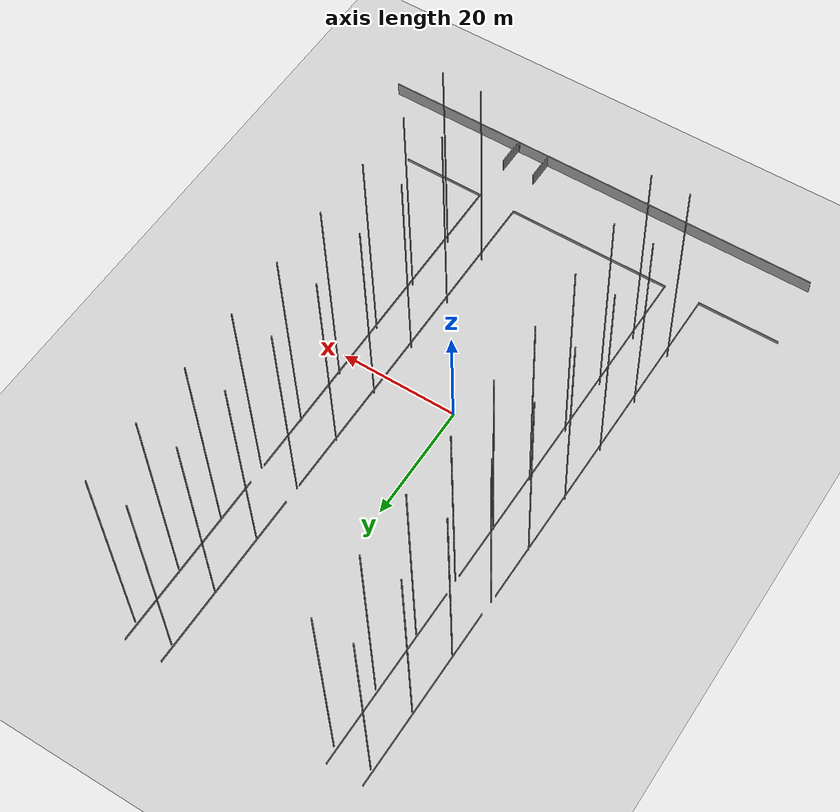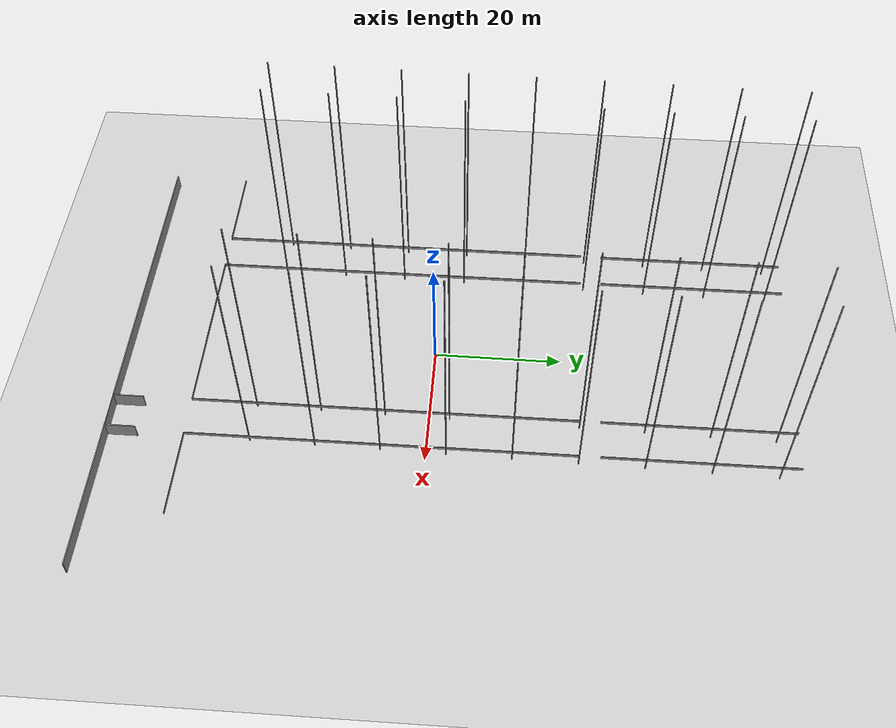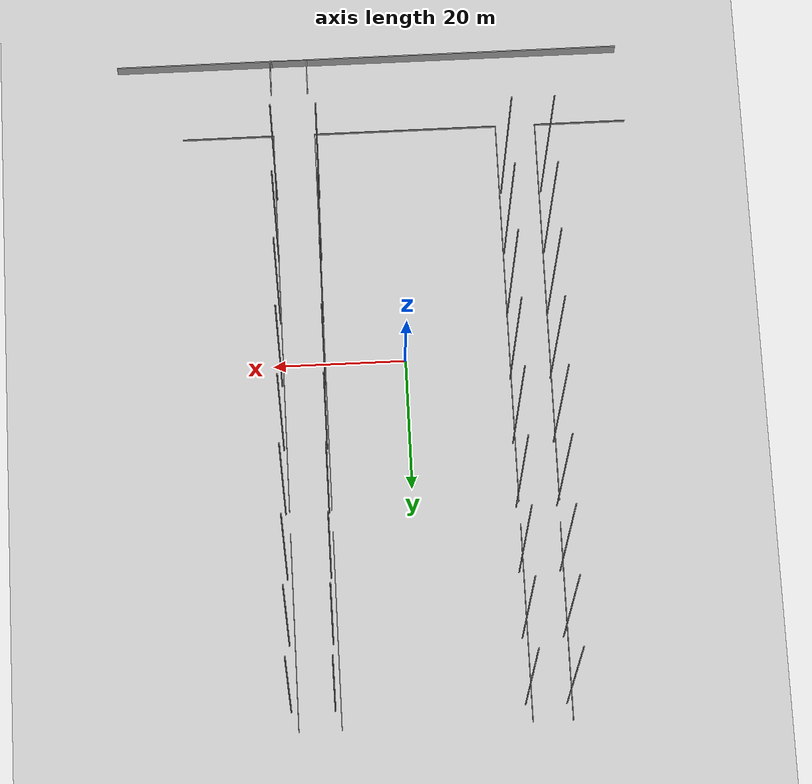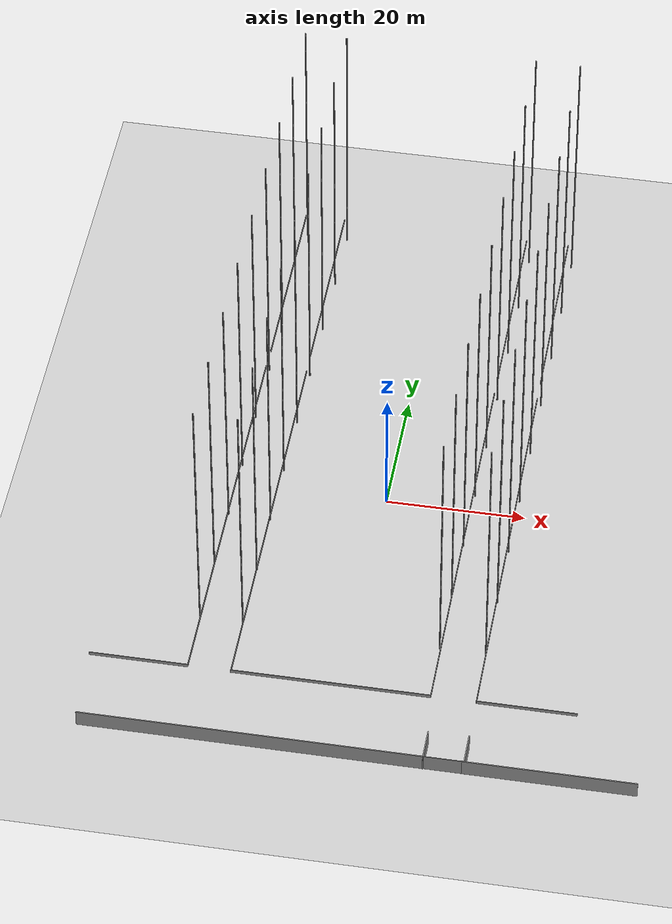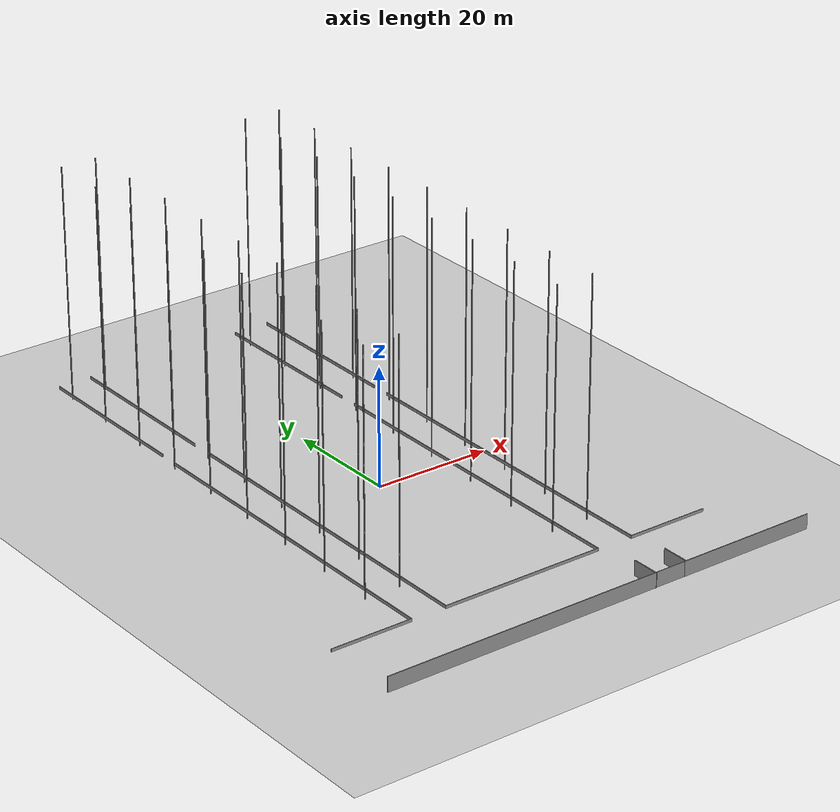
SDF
<sdf version="1.7">
 <world name="default">
  <light name="sun" type="directional">
   <pose>0 0 10 0 -0 0</pose>
   <diffuse>0.8 0.8 0.8 1</diffuse>
   <specular>0.2 0.2 0.2 1</specular>
   <attenuation>
    <range>1000</range>
    <constant>0.9</constant>
    <linear>0.01</linear>
    <quadratic>0.001</quadratic>
   </attenuation>
   <direction>-0.5 0.1 -0.9</direction>
   <spot><inner_angle>0</inner_angle><outer_angle>0</outer_angle><falloff>0</falloff></spot>
  </light>
  <model name="ground_plane">
   <static>1</static>
   <link name="link">
    <collision name="collision">
     <geometry><plane><normal>0 0 1</normal><size>100 100</size></plane></geometry>
     <surface><friction><ode><mu>100</mu><mu2>50</mu2></ode></friction></surface>
    </collision>
    <visual name="visual">
     <cast_shadows>0</cast_shadows>
     <geometry><plane><normal>0 0 1</normal><size>100 100</size></plane></geometry>
     <material>
      <script><uri>file://media/materials/scripts/gazebo.material</uri><name>Gazebo/Grey</name></script>
     </material>
    </visual>
   </link>
  </model>
  <gravity>0 0 -9.8</gravity>
  <magnetic_field>6e-06 2.3e-05 -4.2e-05</magnetic_field>
  <atmosphere type="adiabatic"/>
  <physics type="ode">
   <max_step_size>0.001</max_step_size>
   <real_time_factor>1</real_time_factor>
   <real_time_update_rate>1000</real_time_update_rate>
  </physics>
  <scene><ambient>0.4 0.4 0.4 1</ambient><background>0.7 0.7 0.7 1</background><shadows>1</shadows></scene>
  <audio><device>default</device></audio>
  <spherical_coordinates>
   <surface_model>EARTH_WGS84</surface_model>
   <latitude_deg>0</latitude_deg>
   <longitude_deg>0</longitude_deg>
   <elevation>0</elevation>
   <heading_deg>0</heading_deg>
  </spherical_coordinates>
  <model name="muchang">
   <pose>-2.7147 -13.263 0 0 -0 0</pose>
   <link name="Wall_110">
    <collision name="Wall_110_Collision">
     <geometry><box><size>24 0.15 2.5</size></box></geometry>
     <pose>0 0 1.25 0 -0 0</pose>
    </collision>
    <visual name="Wall_110_Visual">
     <pose>0 0 1.25 0 -0 0</pose>
     <geometry><box><size>24 0.15 2.5</size></box></geometry>
     <material>
      <script><uri>file://media/materials/scripts/gazebo.material</uri><name>Gazebo/Grey</name></script>
      <ambient>1 1 1 1</ambient>
     </material>
     <meta><layer>0</layer></meta>
    </visual>
    <pose>33.0337 -35.6051 0 0 -0 0</pose>
   </link>
   <link name="Wall_113">
    <collision name="Wall_113_Collision">
     <geometry><box><size>14 0.1 0.5</size></box></geometry>
     <pose>0 0 1.25 0 -0 0</pose>
    </collision>
    <visual name="Wall_113_Visual">
     <pose>0 0 1.25 0 -0 0</pose>
     <geometry><box><size>14 0.1 0.5</size></box></geometry>
     <material>
      <script><uri>file://media/materials/scripts/gazebo.material</uri><name>Gazebo/Grey</name></script>
      <ambient>1 1 1 1</ambient>
     </material>
     <meta><layer>0</layer></meta>
    </visual>
    <pose>-26.0749 -23.6284 0 0 -0 0</pose>
   </link>
   <link name="Wall_114">
    <collision name="Wall_114_Collision">
     <geometry><box><size>60 0.1 0.5</size></box></geometry>
     <pose>0 0 1.25 0 -0 0</pose>
    </collision>
    <visual name="Wall_114_Visual">
     <pose>0 0 1.25 0 -0 0</pose>
     <geometry><box><size>60 0.1 0.5</size></box></geometry>
     <material>
      <script><uri>file://media/materials/scripts/gazebo.material</uri><name>Gazebo/Grey</name></script>
      <ambient>1 1 1 1</ambient>
     </material>
     <meta><layer>0</layer></meta>
    </visual>
    <pose>-19.1369 6.41425 0 0 -0 1.5708</pose>
   </link>
   <link name="Wall_117">
    <collision name="Wall_117_Collision">
     <geometry><box><size>60 0.1 0.5</size></box></geometry>
     <pose>0 0 1.25 0 -0 0</pose>
    </collision>
    <visual name="Wall_117_Visual">
     <pose>0 0 1.25 0 -0 0</pose>
     <geometry><box><size>60 0.1 0.5</size></box></geometry>
     <material>
      <script><uri>file://media/materials/scripts/gazebo.material</uri><name>Gazebo/Grey</name></script>
      <ambient>1 1 1 1</ambient>
     </material>
     <meta><layer>0</layer></meta>
    </visual>
    <pose>-13.0627 6.36549 0 0 0 -1.5708</pose>
   </link>
   <link name="Wall_118">
    <collision name="Wall_118_Collision">
     <geometry><box><size>28 0.1 0.5</size></box></geometry>
     <pose>0 0 1.25 0 -0 0</pose>
    </collision>
    <visual name="Wall_118_Visual">
     <pose>0 0 1.25 0 -0 0</pose>
     <geometry><box><size>28 0.1 0.5</size></box></geometry>
     <material>
      <script><uri>file://media/materials/scripts/gazebo.material</uri><name>Gazebo/Grey</name></script>
      <ambient>1 1 1 1</ambient>
     </material>
     <meta><layer>0</layer></meta>
    </visual>
    <pose>0.861755 -23.6284 0 0 -0 0</pose>
   </link>
   <link name="Wall_119">
    <collision name="Wall_119_Collision">
     <geometry><box><size>60 0.1 0.5</size></box></geometry>
     <pose>0 0 1.25 0 -0 0</pose>
    </collision>
    <visual name="Wall_119_Visual">
     <pose>0 0 1.25 0 -0 0</pose>
     <geometry><box><size>60 0.1 0.5</size></box></geometry>
     <material>
      <script><uri>file://media/materials/scripts/gazebo.material</uri><name>Gazebo/Grey</name></script>
      <ambient>1 1 1 1</ambient>
     </material>
     <meta><layer>0</layer></meta>
    </visual>
    <pose>14.8947 6.3456 0 0 -0 1.5708</pose>
   </link>
   <link name="Wall_125">
    <collision name="Wall_125_Collision">
     <geometry><box><size>60 0.1 0.5</size></box></geometry>
     <pose>0 0 1.25 0 -0 0</pose>
    </collision>
    <visual name="Wall_125_Visual">
     <pose>0 0 1.25 0 -0 0</pose>
     <geometry><box><size>60 0.1 0.5</size></box></geometry>
     <material>
      <script><uri>file://media/materials/scripts/gazebo.material</uri><name>Gazebo/Grey</name></script>
      <ambient>1 1 1 1</ambient>
     </material>
     <meta><layer>0</layer></meta>
    </visual>
    <pose>21.2422 6.345 0 0 0 -1.5708</pose>
   </link>
   <link name="Wall_126">
    <collision name="Wall_126_Collision">
     <geometry><box><size>14 0.1 0.5</size></box></geometry>
     <pose>0 0 1.25 0 -0 0</pose>
    </collision>
    <visual name="Wall_126_Visual">
     <pose>0 0 1.25 0 -0 0</pose>
     <geometry><box><size>14 0.1 0.5</size></box></geometry>
     <material>
      <script><uri>file://media/materials/scripts/gazebo.material</uri><name>Gazebo/Grey</name></script>
      <ambient>1 1 1 1</ambient>
     </material>
     <meta><layer>0</layer></meta>
    </visual>
    <pose>28.2337 -23.6284 0 0 -0 0</pose>
   </link>
   <link name="Wall_128">
    <collision name="Wall_128_Collision">
     <geometry><box><size>30 0.1 0.5</size></box></geometry>
     <pose>0 0 1.25 0 -0 0</pose>
    </collision>
    <visual name="Wall_128_Visual">
     <pose>0 0 1.25 0 -0 0</pose>
     <geometry><box><size>30 0.1 0.5</size></box></geometry>
     <material>
      <script><uri>file://media/materials/scripts/gazebo.material</uri><name>Gazebo/Grey</name></script>
      <ambient>1 1 1 1</ambient>
     </material>
     <meta><layer>0</layer></meta>
    </visual>
    <pose>-19.0369 54.7691 0 0 -0 1.5708</pose>
   </link>
   <link name="Wall_149">
    <collision name="Wall_149_Collision">
     <geometry><box><size>30 0.1 0.5</size></box></geometry>
     <pose>0 0 1.25 0 -0 0</pose>
    </collision>
    <visual name="Wall_149_Visual">
     <pose>0 0 1.25 0 -0 0</pose>
     <geometry><box><size>30 0.1 0.5</size></box></geometry>
     <material>
      <script><uri>file://media/materials/scripts/gazebo.material</uri><name>Gazebo/Grey</name></script>
      <ambient>1 1 1 1</ambient>
     </material>
     <meta><layer>0</layer></meta>
    </visual>
    <pose>-13.1062 54.7691 0 0 -0 1.5708</pose>
   </link>
   <link name="Wall_173">
    <collision name="Wall_173_Collision">
     <geometry><box><size>30 0.1 0.5</size></box></geometry>
     <pose>0 0 1.25 0 -0 0</pose>
    </collision>
    <visual name="Wall_173_Visual">
     <pose>0 0 1.25 0 -0 0</pose>
     <geometry><box><size>30 0.1 0.5</size></box></geometry>
     <material>
      <script><uri>file://media/materials/scripts/gazebo.material</uri><name>Gazebo/Grey</name></script>
      <ambient>1 1 1 1</ambient>
     </material>
     <meta><layer>0</layer></meta>
    </visual>
    <pose>14.9012 54.6691 0 0 -0 1.5708</pose>
   </link>
   <link name="Wall_184">
    <collision name="Wall_184_Collision">
     <geometry><box><size>30 0.1 0.5</size></box></geometry>
     <pose>0 0 1.25 0 -0 0</pose>
    </collision>
    <visual name="Wall_184_Visual">
     <pose>0 0 1.25 0 -0 0</pose>
     <geometry><box><size>30 0.1 0.5</size></box></geometry>
     <material>
      <script><uri>file://media/materials/scripts/gazebo.material</uri><name>Gazebo/Grey</name></script>
      <ambient>1 1 1 1</ambient>
     </material>
     <meta><layer>0</layer></meta>
    </visual>
    <pose>21.2422 54.6691 0 0 -0 1.5708</pose>
   </link>
   <link name="Wall_6">
    <collision name="Wall_6_Collision">
     <geometry><box><size>48 0.15 2.5</size></box></geometry>
     <pose>0 0 1.25 0 -0 0</pose>
    </collision>
    <visual name="Wall_6_Visual">
     <pose>0 0 1.25 0 -0 0</pose>
     <geometry><box><size>48 0.15 2.5</size></box></geometry>
     <material>
      <script><uri>file://media/materials/scripts/gazebo.material</uri><name>Gazebo/Grey</name></script>
      <ambient>1 1 1 1</ambient>
     </material>
     <meta><layer>0</layer></meta>
    </visual>
    <pose>-8.3608 -35.6051 0 0 -0 0</pose>
   </link>
   <link name="Wall_7">
    <collision name="Wall_7_Collision">
     <geometry><box><size>4.75 0.15 2.5</size></box></geometry>
     <pose>0 0 1.25 0 -0 0</pose>
    </collision>
    <visual name="Wall_7_Visual">
     <pose>0 0 1.25 0 -0 0</pose>
     <geometry><box><size>4.75 0.15 2.5</size></box></geometry>
     <material>
      <script><uri>file://media/materials/scripts/gazebo.material</uri><name>Gazebo/Grey</name></script>
      <ambient>1 1 1 1</ambient>
     </material>
     <meta><layer>0</layer></meta>
    </visual>
    <pose>15.6997 -33.2772 -0.088121 0 0 -1.5708</pose>
   </link>
   <link name="Wall_8">
    <collision name="Wall_8_Collision">
     <geometry><box><size>5.5 0.1 2.5</size></box></geometry>
     <pose>0 0 1.25 0 -0 0</pose>
    </collision>
    <visual name="Wall_8_Visual">
     <pose>0 0 1.25 0 -0 0</pose>
     <geometry><box><size>5.5 0.1 2.5</size></box></geometry>
     <material>
      <script><uri>file://media/materials/scripts/gazebo.material</uri><name>Gazebo/Grey</name></script>
      <ambient>1 1 1 1</ambient>
     </material>
     <meta><layer>0</layer></meta>
    </visual>
    <pose>18.5043 -35.6051 0 0 -0 0</pose>
   </link>
   <link name="Wall_9">
    <collision name="Wall_9_Collision">
     <geometry><box><size>4.75 0.15 2.5</size></box></geometry>
     <pose>0 0 1.25 0 -0 0</pose>
    </collision>
    <visual name="Wall_9_Visual">
     <pose>0 0 1.25 0 -0 0</pose>
     <geometry><box><size>4.75 0.15 2.5</size></box></geometry>
     <material>
      <script><uri>file://media/materials/scripts/gazebo.material</uri><name>Gazebo/Grey</name></script>
      <ambient>1 1 1 1</ambient>
     </material>
     <meta><layer>0</layer></meta>
    </visual>
    <pose>21.3422 -33.2718 0 0 -0 1.5708</pose>
   </link>
   <static>1</static>
  </model>
  <model name="muchang_s">
   <link name="link_0">
    <inertial>
     <mass>1</mass>
     <inertia><ixx>0.145833</ixx><ixy>0</ixy><ixz>0</ixz><iyy>0.145833</iyy><iyz>0</iyz><izz>0.125</izz></inertia>
    </inertial>
    <pose>-3.71609 27.7468 1.31427 0 -0 0</pose>
    <visual name="visual">
     <geometry><cylinder><radius>0.1</radius><length>40</length></cylinder></geometry>
     <material>
      <lighting>1</lighting>
      <script><uri>file://media/materials/scripts/gazebo.material</uri><name>Gazebo/Grey</name></script>
      <shader type="pixel"><normal_map>__default__</normal_map></shader>
      <ambient>0.3 0.3 0.3 1</ambient>
      <diffuse>0.7 0.7 0.7 1</diffuse>
      <specular>0.01 0.01 0.01 1</specular>
      <emissive>0 0 0 1</emissive>
     </material>
    </visual>
    <collision name="collision">
     <geometry><cylinder><radius>0.1</radius><length>40</length></cylinder></geometry>
     <surface>
      <friction>
       <ode><mu>1</mu><mu2>1</mu2><fdir1>0 0 0</fdir1><slip1>0</slip1><slip2>0</slip2></ode>
       <torsional>
        <coefficient>1</coefficient>
        <patch_radius>0</patch_radius>
        <surface_radius>0</surface_radius>
        <use_patch_radius>1</use_patch_radius>
        <ode><slip>0</slip></ode>
       </torsional>
      </friction>
      <bounce><restitution_coefficient>0</restitution_coefficient><threshold>1e+06</threshold></bounce>
      <contact>
       <collide_without_contact>0</collide_without_contact>
       <collide_without_contact_bitmask>1</collide_without_contact_bitmask>
       <collide_bitmask>1</collide_bitmask>
       <ode>
        <soft_cfm>0</soft_cfm>
        <soft_erp>0.2</soft_erp>
        <kp>1e+13</kp>
        <kd>1</kd>
        <max_vel>0.01</max_vel>
        <min_depth>0</min_depth>
       </ode>
       <bullet>
        <split_impulse>1</split_impulse>
        <split_impulse_penetration_threshold>-0.01</split_impulse_penetration_threshold>
        <soft_cfm>0</soft_cfm>
        <soft_erp>0.2</soft_erp>
        <kp>1e+13</kp>
        <kd>1</kd>
       </bullet>
      </contact>
     </surface>
    </collision>
   </link>
   <link name="link_0_clone">
    <inertial>
     <mass>1</mass>
     <inertia><ixx>0.145833</ixx><ixy>0</ixy><ixz>0</ixz><iyy>0.145833</iyy><iyz>0</iyz><izz>0.125</izz></inertia>
    </inertial>
    <pose>-3.71609 17.7468 1.31427 0 -0 0</pose>
    <visual name="visual">
     <geometry><cylinder><radius>0.1</radius><length>40</length></cylinder></geometry>
     <material>
      <lighting>1</lighting>
      <script><uri>file://media/materials/scripts/gazebo.material</uri><name>Gazebo/Grey</name></script>
      <shader type="pixel"><normal_map>__default__</normal_map></shader>
      <ambient>0.3 0.3 0.3 1</ambient>
      <diffuse>0.7 0.7 0.7 1</diffuse>
      <specular>0.01 0.01 0.01 1</specular>
      <emissive>0 0 0 1</emissive>
     </material>
    </visual>
    <collision name="collision">
     <geometry><cylinder><radius>0.1</radius><length>40</length></cylinder></geometry>
     <surface>
      <friction>
       <ode><mu>1</mu><mu2>1</mu2><fdir1>0 0 0</fdir1><slip1>0</slip1><slip2>0</slip2></ode>
       <torsional>
        <coefficient>1</coefficient>
        <patch_radius>0</patch_radius>
        <surface_radius>0</surface_radius>
        <use_patch_radius>1</use_patch_radius>
        <ode><slip>0</slip></ode>
       </torsional>
      </friction>
      <bounce><restitution_coefficient>0</restitution_coefficient><threshold>1e+06</threshold></bounce>
      <contact>
       <collide_without_contact>0</collide_without_contact>
       <collide_without_contact_bitmask>1</collide_without_contact_bitmask>
       <collide_bitmask>1</collide_bitmask>
       <ode>
        <soft_cfm>0</soft_cfm>
        <soft_erp>0.2</soft_erp>
        <kp>1e+13</kp>
        <kd>1</kd>
        <max_vel>0.01</max_vel>
        <min_depth>0</min_depth>
       </ode>
       <bullet>
        <split_impulse>1</split_impulse>
        <split_impulse_penetration_threshold>-0.01</split_impulse_penetration_threshold>
        <soft_cfm>0</soft_cfm>
        <soft_erp>0.2</soft_erp>
        <kp>1e+13</kp>
        <kd>1</kd>
       </bullet>
      </contact>
     </surface>
    </collision>
   </link>
   <link name="link_0_clone_clone">
    <inertial>
     <mass>1</mass>
     <inertia><ixx>0.145833</ixx><ixy>0</ixy><ixz>0</ixz><iyy>0.145833</iyy><iyz>0</iyz><izz>0.125</izz></inertia>
    </inertial>
    <pose>-3.71609 37.7468 1.31427 0 -0 0</pose>
    <visual name="visual">
     <geometry><cylinder><radius>0.1</radius><length>40</length></cylinder></geometry>
     <material>
      <lighting>1</lighting>
      <script><uri>file://media/materials/scripts/gazebo.material</uri><name>Gazebo/Grey</name></script>
      <shader type="pixel"><normal_map>__default__</normal_map></shader>
      <ambient>0.3 0.3 0.3 1</ambient>
      <diffuse>0.7 0.7 0.7 1</diffuse>
      <specular>0.01 0.01 0.01 1</specular>
      <emissive>0 0 0 1</emissive>
     </material>
    </visual>
    <collision name="collision">
     <geometry><cylinder><radius>0.1</radius><length>40</length></cylinder></geometry>
     <surface>
      <friction>
       <ode><mu>1</mu><mu2>1</mu2><fdir1>0 0 0</fdir1><slip1>0</slip1><slip2>0</slip2></ode>
       <torsional>
        <coefficient>1</coefficient>
        <patch_radius>0</patch_radius>
        <surface_radius>0</surface_radius>
        <use_patch_radius>1</use_patch_radius>
        <ode><slip>0</slip></ode>
       </torsional>
      </friction>
      <bounce><restitution_coefficient>0</restitution_coefficient><threshold>1e+06</threshold></bounce>
      <contact>
       <collide_without_contact>0</collide_without_contact>
       <collide_without_contact_bitmask>1</collide_without_contact_bitmask>
       <collide_bitmask>1</collide_bitmask>
       <ode>
        <soft_cfm>0</soft_cfm>
        <soft_erp>0.2</soft_erp>
        <kp>1e+13</kp>
        <kd>1</kd>
        <max_vel>0.01</max_vel>
        <min_depth>0</min_depth>
       </ode>
       <bullet>
        <split_impulse>1</split_impulse>
        <split_impulse_penetration_threshold>-0.01</split_impulse_penetration_threshold>
        <soft_cfm>0</soft_cfm>
        <soft_erp>0.2</soft_erp>
        <kp>1e+13</kp>
        <kd>1</kd>
       </bullet>
      </contact>
     </surface>
    </collision>
   </link>
   <link name="link_0_clone_clone_0">
    <inertial>
     <mass>1</mass>
     <inertia><ixx>0.145833</ixx><ixy>0</ixy><ixz>0</ixz><iyy>0.145833</iyy><iyz>0</iyz><izz>0.125</izz></inertia>
    </inertial>
    <pose>2.77174 17.7468 1.31427 0 -0 0</pose>
    <visual name="visual">
     <geometry><cylinder><radius>0.1</radius><length>40</length></cylinder></geometry>
     <material>
      <lighting>1</lighting>
      <script><uri>file://media/materials/scripts/gazebo.material</uri><name>Gazebo/Grey</name></script>
      <shader type="pixel"><normal_map>__default__</normal_map></shader>
      <ambient>0.3 0.3 0.3 1</ambient>
      <diffuse>0.7 0.7 0.7 1</diffuse>
      <specular>0.01 0.01 0.01 1</specular>
      <emissive>0 0 0 1</emissive>
     </material>
    </visual>
    <collision name="collision">
     <geometry><cylinder><radius>0.1</radius><length>40</length></cylinder></geometry>
     <surface>
      <friction>
       <ode><mu>1</mu><mu2>1</mu2><fdir1>0 0 0</fdir1><slip1>0</slip1><slip2>0</slip2></ode>
       <torsional>
        <coefficient>1</coefficient>
        <patch_radius>0</patch_radius>
        <surface_radius>0</surface_radius>
        <use_patch_radius>1</use_patch_radius>
        <ode><slip>0</slip></ode>
       </torsional>
      </friction>
      <bounce><restitution_coefficient>0</restitution_coefficient><threshold>1e+06</threshold></bounce>
      <contact>
       <collide_without_contact>0</collide_without_contact>
       <collide_without_contact_bitmask>1</collide_without_contact_bitmask>
       <collide_bitmask>1</collide_bitmask>
       <ode>
        <soft_cfm>0</soft_cfm>
        <soft_erp>0.2</soft_erp>
        <kp>1e+13</kp>
        <kd>1</kd>
        <max_vel>0.01</max_vel>
        <min_depth>0</min_depth>
       </ode>
       <bullet>
        <split_impulse>1</split_impulse>
        <split_impulse_penetration_threshold>-0.01</split_impulse_penetration_threshold>
        <soft_cfm>0</soft_cfm>
        <soft_erp>0.2</soft_erp>
        <kp>1e+13</kp>
        <kd>1</kd>
       </bullet>
      </contact>
     </surface>
    </collision>
   </link>
   <link name="link_0_clone_clone_0_clone">
    <inertial>
     <mass>1</mass>
     <inertia><ixx>0.145833</ixx><ixy>0</ixy><ixz>0</ixz><iyy>0.145833</iyy><iyz>0</iyz><izz>0.125</izz></inertia>
    </inertial>
    <pose>2.77174 27.7468 1.31427 0 -0 0</pose>
    <visual name="visual">
     <geometry><cylinder><radius>0.1</radius><length>40</length></cylinder></geometry>
     <material>
      <lighting>1</lighting>
      <script><uri>file://media/materials/scripts/gazebo.material</uri><name>Gazebo/Grey</name></script>
      <shader type="pixel"><normal_map>__default__</normal_map></shader>
      <ambient>0.3 0.3 0.3 1</ambient>
      <diffuse>0.7 0.7 0.7 1</diffuse>
      <specular>0.01 0.01 0.01 1</specular>
      <emissive>0 0 0 1</emissive>
     </material>
    </visual>
    <collision name="collision">
     <geometry><cylinder><radius>0.1</radius><length>40</length></cylinder></geometry>
     <surface>
      <friction>
       <ode><mu>1</mu><mu2>1</mu2><fdir1>0 0 0</fdir1><slip1>0</slip1><slip2>0</slip2></ode>
       <torsional>
        <coefficient>1</coefficient>
        <patch_radius>0</patch_radius>
        <surface_radius>0</surface_radius>
        <use_patch_radius>1</use_patch_radius>
        <ode><slip>0</slip></ode>
       </torsional>
      </friction>
      <bounce><restitution_coefficient>0</restitution_coefficient><threshold>1e+06</threshold></bounce>
      <contact>
       <collide_without_contact>0</collide_without_contact>
       <collide_without_contact_bitmask>1</collide_without_contact_bitmask>
       <collide_bitmask>1</collide_bitmask>
       <ode>
        <soft_cfm>0</soft_cfm>
        <soft_erp>0.2</soft_erp>
        <kp>1e+13</kp>
        <kd>1</kd>
        <max_vel>0.01</max_vel>
        <min_depth>0</min_depth>
       </ode>
       <bullet>
        <split_impulse>1</split_impulse>
        <split_impulse_penetration_threshold>-0.01</split_impulse_penetration_threshold>
        <soft_cfm>0</soft_cfm>
        <soft_erp>0.2</soft_erp>
        <kp>1e+13</kp>
        <kd>1</kd>
       </bullet>
      </contact>
     </surface>
    </collision>
   </link>
   <link name="link_0_clone_clone_0_clone_1">
    <inertial>
     <mass>1</mass>
     <inertia><ixx>0.145833</ixx><ixy>0</ixy><ixz>0</ixz><iyy>0.145833</iyy><iyz>0</iyz><izz>0.125</izz></inertia>
    </inertial>
    <pose>2.77174 37.7468 1.31427 0 -0 0</pose>
    <visual name="visual">
     <geometry><cylinder><radius>0.1</radius><length>40</length></cylinder></geometry>
     <material>
      <lighting>1</lighting>
      <script><uri>file://media/materials/scripts/gazebo.material</uri><name>Gazebo/Grey</name></script>
      <shader type="pixel"><normal_map>__default__</normal_map></shader>
      <ambient>0.3 0.3 0.3 1</ambient>
      <diffuse>0.7 0.7 0.7 1</diffuse>
      <specular>0.01 0.01 0.01 1</specular>
      <emissive>0 0 0 1</emissive>
     </material>
    </visual>
    <collision name="collision">
     <geometry><cylinder><radius>0.1</radius><length>40</length></cylinder></geometry>
     <surface>
      <friction>
       <ode><mu>1</mu><mu2>1</mu2><fdir1>0 0 0</fdir1><slip1>0</slip1><slip2>0</slip2></ode>
       <torsional>
        <coefficient>1</coefficient>
        <patch_radius>0</patch_radius>
        <surface_radius>0</surface_radius>
        <use_patch_radius>1</use_patch_radius>
        <ode><slip>0</slip></ode>
       </torsional>
      </friction>
      <bounce><restitution_coefficient>0</restitution_coefficient><threshold>1e+06</threshold></bounce>
      <contact>
       <collide_without_contact>0</collide_without_contact>
       <collide_without_contact_bitmask>1</collide_without_contact_bitmask>
       <collide_bitmask>1</collide_bitmask>
       <ode>
        <soft_cfm>0</soft_cfm>
        <soft_erp>0.2</soft_erp>
        <kp>1e+13</kp>
        <kd>1</kd>
        <max_vel>0.01</max_vel>
        <min_depth>0</min_depth>
       </ode>
       <bullet>
        <split_impulse>1</split_impulse>
        <split_impulse_penetration_threshold>-0.01</split_impulse_penetration_threshold>
        <soft_cfm>0</soft_cfm>
        <soft_erp>0.2</soft_erp>
        <kp>1e+13</kp>
        <kd>1</kd>
       </bullet>
      </contact>
     </surface>
    </collision>
   </link>
   <link name="link_0_clone_clone_0_clone_2">
    <inertial>
     <mass>1</mass>
     <inertia><ixx>0.145833</ixx><ixy>0</ixy><ixz>0</ixz><iyy>0.145833</iyy><iyz>0</iyz><izz>0.125</izz></inertia>
    </inertial>
    <pose>2.77174 47.7468 1.31427 0 -0 0</pose>
    <visual name="visual">
     <geometry><cylinder><radius>0.1</radius><length>40</length></cylinder></geometry>
     <material>
      <lighting>1</lighting>
      <script><uri>file://media/materials/scripts/gazebo.material</uri><name>Gazebo/Grey</name></script>
      <shader type="pixel"><normal_map>__default__</normal_map></shader>
      <ambient>0.3 0.3 0.3 1</ambient>
      <diffuse>0.7 0.7 0.7 1</diffuse>
      <specular>0.01 0.01 0.01 1</specular>
      <emissive>0 0 0 1</emissive>
     </material>
    </visual>
    <collision name="collision">
     <geometry><cylinder><radius>0.1</radius><length>40</length></cylinder></geometry>
     <surface>
      <friction>
       <ode><mu>1</mu><mu2>1</mu2><fdir1>0 0 0</fdir1><slip1>0</slip1><slip2>0</slip2></ode>
       <torsional>
        <coefficient>1</coefficient>
        <patch_radius>0</patch_radius>
        <surface_radius>0</surface_radius>
        <use_patch_radius>1</use_patch_radius>
        <ode><slip>0</slip></ode>
       </torsional>
      </friction>
      <bounce><restitution_coefficient>0</restitution_coefficient><threshold>1e+06</threshold></bounce>
      <contact>
       <collide_without_contact>0</collide_without_contact>
       <collide_without_contact_bitmask>1</collide_without_contact_bitmask>
       <collide_bitmask>1</collide_bitmask>
       <ode>
        <soft_cfm>0</soft_cfm>
        <soft_erp>0.2</soft_erp>
        <kp>1e+13</kp>
        <kd>1</kd>
        <max_vel>0.01</max_vel>
        <min_depth>0</min_depth>
       </ode>
       <bullet>
        <split_impulse>1</split_impulse>
        <split_impulse_penetration_threshold>-0.01</split_impulse_penetration_threshold>
        <soft_cfm>0</soft_cfm>
        <soft_erp>0.2</soft_erp>
        <kp>1e+13</kp>
        <kd>1</kd>
       </bullet>
      </contact>
     </surface>
    </collision>
   </link>
   <link name="link_0_clone_clone_0_clone_3">
    <inertial>
     <mass>1</mass>
     <inertia><ixx>0.145833</ixx><ixy>0</ixy><ixz>0</ixz><iyy>0.145833</iyy><iyz>0</iyz><izz>0.125</izz></inertia>
    </inertial>
    <pose>2.77174 57.7468 1.31427 0 -0 0</pose>
    <visual name="visual">
     <geometry><cylinder><radius>0.1</radius><length>40</length></cylinder></geometry>
     <material>
      <lighting>1</lighting>
      <script><uri>file://media/materials/scripts/gazebo.material</uri><name>Gazebo/Grey</name></script>
      <shader type="pixel"><normal_map>__default__</normal_map></shader>
      <ambient>0.3 0.3 0.3 1</ambient>
      <diffuse>0.7 0.7 0.7 1</diffuse>
      <specular>0.01 0.01 0.01 1</specular>
      <emissive>0 0 0 1</emissive>
     </material>
    </visual>
    <collision name="collision">
     <geometry><cylinder><radius>0.1</radius><length>40</length></cylinder></geometry>
     <surface>
      <friction>
       <ode><mu>1</mu><mu2>1</mu2><fdir1>0 0 0</fdir1><slip1>0</slip1><slip2>0</slip2></ode>
       <torsional>
        <coefficient>1</coefficient>
        <patch_radius>0</patch_radius>
        <surface_radius>0</surface_radius>
        <use_patch_radius>1</use_patch_radius>
        <ode><slip>0</slip></ode>
       </torsional>
      </friction>
      <bounce><restitution_coefficient>0</restitution_coefficient><threshold>1e+06</threshold></bounce>
      <contact>
       <collide_without_contact>0</collide_without_contact>
       <collide_without_contact_bitmask>1</collide_without_contact_bitmask>
       <collide_bitmask>1</collide_bitmask>
       <ode>
        <soft_cfm>0</soft_cfm>
        <soft_erp>0.2</soft_erp>
        <kp>1e+13</kp>
        <kd>1</kd>
        <max_vel>0.01</max_vel>
        <min_depth>0</min_depth>
       </ode>
       <bullet>
        <split_impulse>1</split_impulse>
        <split_impulse_penetration_threshold>-0.01</split_impulse_penetration_threshold>
        <soft_cfm>0</soft_cfm>
        <soft_erp>0.2</soft_erp>
        <kp>1e+13</kp>
        <kd>1</kd>
       </bullet>
      </contact>
     </surface>
    </collision>
   </link>
   <link name="link_0_clone_clone_0_clone_4">
    <inertial>
     <mass>1</mass>
     <inertia><ixx>0.145833</ixx><ixy>0</ixy><ixz>0</ixz><iyy>0.145833</iyy><iyz>0</iyz><izz>0.125</izz></inertia>
    </inertial>
    <pose>2.77174 67.7468 1.31427 0 -0 0</pose>
    <visual name="visual">
     <geometry><cylinder><radius>0.1</radius><length>40</length></cylinder></geometry>
     <material>
      <lighting>1</lighting>
      <script><uri>file://media/materials/scripts/gazebo.material</uri><name>Gazebo/Grey</name></script>
      <shader type="pixel"><normal_map>__default__</normal_map></shader>
      <ambient>0.3 0.3 0.3 1</ambient>
      <diffuse>0.7 0.7 0.7 1</diffuse>
      <specular>0.01 0.01 0.01 1</specular>
      <emissive>0 0 0 1</emissive>
     </material>
    </visual>
    <collision name="collision">
     <geometry><cylinder><radius>0.1</radius><length>40</length></cylinder></geometry>
     <surface>
      <friction>
       <ode><mu>1</mu><mu2>1</mu2><fdir1>0 0 0</fdir1><slip1>0</slip1><slip2>0</slip2></ode>
       <torsional>
        <coefficient>1</coefficient>
        <patch_radius>0</patch_radius>
        <surface_radius>0</surface_radius>
        <use_patch_radius>1</use_patch_radius>
        <ode><slip>0</slip></ode>
       </torsional>
      </friction>
      <bounce><restitution_coefficient>0</restitution_coefficient><threshold>1e+06</threshold></bounce>
      <contact>
       <collide_without_contact>0</collide_without_contact>
       <collide_without_contact_bitmask>1</collide_without_contact_bitmask>
       <collide_bitmask>1</collide_bitmask>
       <ode>
        <soft_cfm>0</soft_cfm>
        <soft_erp>0.2</soft_erp>
        <kp>1e+13</kp>
        <kd>1</kd>
        <max_vel>0.01</max_vel>
        <min_depth>0</min_depth>
       </ode>
       <bullet>
        <split_impulse>1</split_impulse>
        <split_impulse_penetration_threshold>-0.01</split_impulse_penetration_threshold>
        <soft_cfm>0</soft_cfm>
        <soft_erp>0.2</soft_erp>
        <kp>1e+13</kp>
        <kd>1</kd>
       </bullet>
      </contact>
     </surface>
    </collision>
   </link>
   <link name="link_0_clone_clone_0_clone_5">
    <inertial>
     <mass>1</mass>
     <inertia><ixx>0.145833</ixx><ixy>0</ixy><ixz>0</ixz><iyy>0.145833</iyy><iyz>0</iyz><izz>0.125</izz></inertia>
    </inertial>
    <pose>2.77174 77.7468 1.31427 0 -0 0</pose>
    <visual name="visual">
     <geometry><cylinder><radius>0.1</radius><length>40</length></cylinder></geometry>
     <material>
      <lighting>1</lighting>
      <script><uri>file://media/materials/scripts/gazebo.material</uri><name>Gazebo/Grey</name></script>
      <shader type="pixel"><normal_map>__default__</normal_map></shader>
      <ambient>0.3 0.3 0.3 1</ambient>
      <diffuse>0.7 0.7 0.7 1</diffuse>
      <specular>0.01 0.01 0.01 1</specular>
      <emissive>0 0 0 1</emissive>
     </material>
    </visual>
    <collision name="collision">
     <geometry><cylinder><radius>0.1</radius><length>40</length></cylinder></geometry>
     <surface>
      <friction>
       <ode><mu>1</mu><mu2>1</mu2><fdir1>0 0 0</fdir1><slip1>0</slip1><slip2>0</slip2></ode>
       <torsional>
        <coefficient>1</coefficient>
        <patch_radius>0</patch_radius>
        <surface_radius>0</surface_radius>
        <use_patch_radius>1</use_patch_radius>
        <ode><slip>0</slip></ode>
       </torsional>
      </friction>
      <bounce><restitution_coefficient>0</restitution_coefficient><threshold>1e+06</threshold></bounce>
      <contact>
       <collide_without_contact>0</collide_without_contact>
       <collide_without_contact_bitmask>1</collide_without_contact_bitmask>
       <collide_bitmask>1</collide_bitmask>
       <ode>
        <soft_cfm>0</soft_cfm>
        <soft_erp>0.2</soft_erp>
        <kp>1e+13</kp>
        <kd>1</kd>
        <max_vel>0.01</max_vel>
        <min_depth>0</min_depth>
       </ode>
       <bullet>
        <split_impulse>1</split_impulse>
        <split_impulse_penetration_threshold>-0.01</split_impulse_penetration_threshold>
        <soft_cfm>0</soft_cfm>
        <soft_erp>0.2</soft_erp>
        <kp>1e+13</kp>
        <kd>1</kd>
       </bullet>
      </contact>
     </surface>
    </collision>
   </link>
   <link name="link_0_clone_clone_0_clone_6">
    <inertial>
     <mass>1</mass>
     <inertia><ixx>0.145833</ixx><ixy>0</ixy><ixz>0</ixz><iyy>0.145833</iyy><iyz>0</iyz><izz>0.125</izz></inertia>
    </inertial>
    <pose>2.77174 87.7468 1.31427 0 -0 0</pose>
    <visual name="visual">
     <geometry><cylinder><radius>0.1</radius><length>40</length></cylinder></geometry>
     <material>
      <lighting>1</lighting>
      <script><uri>file://media/materials/scripts/gazebo.material</uri><name>Gazebo/Grey</name></script>
      <shader type="pixel"><normal_map>__default__</normal_map></shader>
      <ambient>0.3 0.3 0.3 1</ambient>
      <diffuse>0.7 0.7 0.7 1</diffuse>
      <specular>0.01 0.01 0.01 1</specular>
      <emissive>0 0 0 1</emissive>
     </material>
    </visual>
    <collision name="collision">
     <geometry><cylinder><radius>0.1</radius><length>40</length></cylinder></geometry>
     <surface>
      <friction>
       <ode><mu>1</mu><mu2>1</mu2><fdir1>0 0 0</fdir1><slip1>0</slip1><slip2>0</slip2></ode>
       <torsional>
        <coefficient>1</coefficient>
        <patch_radius>0</patch_radius>
        <surface_radius>0</surface_radius>
        <use_patch_radius>1</use_patch_radius>
        <ode><slip>0</slip></ode>
       </torsional>
      </friction>
      <bounce><restitution_coefficient>0</restitution_coefficient><threshold>1e+06</threshold></bounce>
      <contact>
       <collide_without_contact>0</collide_without_contact>
       <collide_without_contact_bitmask>1</collide_without_contact_bitmask>
       <collide_bitmask>1</collide_bitmask>
       <ode>
        <soft_cfm>0</soft_cfm>
        <soft_erp>0.2</soft_erp>
        <kp>1e+13</kp>
        <kd>1</kd>
        <max_vel>0.01</max_vel>
        <min_depth>0</min_depth>
       </ode>
       <bullet>
        <split_impulse>1</split_impulse>
        <split_impulse_penetration_threshold>-0.01</split_impulse_penetration_threshold>
        <soft_cfm>0</soft_cfm>
        <soft_erp>0.2</soft_erp>
        <kp>1e+13</kp>
        <kd>1</kd>
       </bullet>
      </contact>
     </surface>
    </collision>
   </link>
   <link name="link_0_clone_clone_0_clone_7">
    <inertial>
     <mass>1</mass>
     <inertia><ixx>0.145833</ixx><ixy>0</ixy><ixz>0</ixz><iyy>0.145833</iyy><iyz>0</iyz><izz>0.125</izz></inertia>
    </inertial>
    <pose>2.77174 97.7468 1.31427 0 -0 0</pose>
    <visual name="visual">
     <geometry><cylinder><radius>0.1</radius><length>40</length></cylinder></geometry>
     <material>
      <lighting>1</lighting>
      <script><uri>file://media/materials/scripts/gazebo.material</uri><name>Gazebo/Grey</name></script>
      <shader type="pixel"><normal_map>__default__</normal_map></shader>
      <ambient>0.3 0.3 0.3 1</ambient>
      <diffuse>0.7 0.7 0.7 1</diffuse>
      <specular>0.01 0.01 0.01 1</specular>
      <emissive>0 0 0 1</emissive>
     </material>
    </visual>
    <collision name="collision">
     <geometry><cylinder><radius>0.1</radius><length>40</length></cylinder></geometry>
     <surface>
      <friction>
       <ode><mu>1</mu><mu2>1</mu2><fdir1>0 0 0</fdir1><slip1>0</slip1><slip2>0</slip2></ode>
       <torsional>
        <coefficient>1</coefficient>
        <patch_radius>0</patch_radius>
        <surface_radius>0</surface_radius>
        <use_patch_radius>1</use_patch_radius>
        <ode><slip>0</slip></ode>
       </torsional>
      </friction>
      <bounce><restitution_coefficient>0</restitution_coefficient><threshold>1e+06</threshold></bounce>
      <contact>
       <collide_without_contact>0</collide_without_contact>
       <collide_without_contact_bitmask>1</collide_without_contact_bitmask>
       <collide_bitmask>1</collide_bitmask>
       <ode>
        <soft_cfm>0</soft_cfm>
        <soft_erp>0.2</soft_erp>
        <kp>1e+13</kp>
        <kd>1</kd>
        <max_vel>0.01</max_vel>
        <min_depth>0</min_depth>
       </ode>
       <bullet>
        <split_impulse>1</split_impulse>
        <split_impulse_penetration_threshold>-0.01</split_impulse_penetration_threshold>
        <soft_cfm>0</soft_cfm>
        <soft_erp>0.2</soft_erp>
        <kp>1e+13</kp>
        <kd>1</kd>
       </bullet>
      </contact>
     </surface>
    </collision>
   </link>
   <link name="link_0_clone_clone_1">
    <inertial>
     <mass>1</mass>
     <inertia><ixx>0.145833</ixx><ixy>0</ixy><ixz>0</ixz><iyy>0.145833</iyy><iyz>0</iyz><izz>0.125</izz></inertia>
    </inertial>
    <pose>-37.8115 17.7468 1.31427 0 -0 0</pose>
    <visual name="visual">
     <geometry><cylinder><radius>0.1</radius><length>40</length></cylinder></geometry>
     <material>
      <lighting>1</lighting>
      <script><uri>file://media/materials/scripts/gazebo.material</uri><name>Gazebo/Grey</name></script>
      <shader type="pixel"><normal_map>__default__</normal_map></shader>
      <ambient>0.3 0.3 0.3 1</ambient>
      <diffuse>0.7 0.7 0.7 1</diffuse>
      <specular>0.01 0.01 0.01 1</specular>
      <emissive>0 0 0 1</emissive>
     </material>
    </visual>
    <collision name="collision">
     <geometry><cylinder><radius>0.1</radius><length>40</length></cylinder></geometry>
     <surface>
      <friction>
       <ode><mu>1</mu><mu2>1</mu2><fdir1>0 0 0</fdir1><slip1>0</slip1><slip2>0</slip2></ode>
       <torsional>
        <coefficient>1</coefficient>
        <patch_radius>0</patch_radius>
        <surface_radius>0</surface_radius>
        <use_patch_radius>1</use_patch_radius>
        <ode><slip>0</slip></ode>
       </torsional>
      </friction>
      <bounce><restitution_coefficient>0</restitution_coefficient><threshold>1e+06</threshold></bounce>
      <contact>
       <collide_without_contact>0</collide_without_contact>
       <collide_without_contact_bitmask>1</collide_without_contact_bitmask>
       <collide_bitmask>1</collide_bitmask>
       <ode>
        <soft_cfm>0</soft_cfm>
        <soft_erp>0.2</soft_erp>
        <kp>1e+13</kp>
        <kd>1</kd>
        <max_vel>0.01</max_vel>
        <min_depth>0</min_depth>
       </ode>
       <bullet>
        <split_impulse>1</split_impulse>
        <split_impulse_penetration_threshold>-0.01</split_impulse_penetration_threshold>
        <soft_cfm>0</soft_cfm>
        <soft_erp>0.2</soft_erp>
        <kp>1e+13</kp>
        <kd>1</kd>
       </bullet>
      </contact>
     </surface>
    </collision>
   </link>
   <link name="link_0_clone_clone_1_clone">
    <inertial>
     <mass>1</mass>
     <inertia><ixx>0.145833</ixx><ixy>0</ixy><ixz>0</ixz><iyy>0.145833</iyy><iyz>0</iyz><izz>0.125</izz></inertia>
    </inertial>
    <pose>-31.6959 17.7468 1.31427 0 -0 0</pose>
    <visual name="visual">
     <geometry><cylinder><radius>0.1</radius><length>40</length></cylinder></geometry>
     <material>
      <lighting>1</lighting>
      <script><uri>file://media/materials/scripts/gazebo.material</uri><name>Gazebo/Grey</name></script>
      <shader type="pixel"><normal_map>__default__</normal_map></shader>
      <ambient>0.3 0.3 0.3 1</ambient>
      <diffuse>0.7 0.7 0.7 1</diffuse>
      <specular>0.01 0.01 0.01 1</specular>
      <emissive>0 0 0 1</emissive>
     </material>
    </visual>
    <collision name="collision">
     <geometry><cylinder><radius>0.1</radius><length>40</length></cylinder></geometry>
     <surface>
      <friction>
       <ode><mu>1</mu><mu2>1</mu2><fdir1>0 0 0</fdir1><slip1>0</slip1><slip2>0</slip2></ode>
       <torsional>
        <coefficient>1</coefficient>
        <patch_radius>0</patch_radius>
        <surface_radius>0</surface_radius>
        <use_patch_radius>1</use_patch_radius>
        <ode><slip>0</slip></ode>
       </torsional>
      </friction>
      <bounce><restitution_coefficient>0</restitution_coefficient><threshold>1e+06</threshold></bounce>
      <contact>
       <collide_without_contact>0</collide_without_contact>
       <collide_without_contact_bitmask>1</collide_without_contact_bitmask>
       <collide_bitmask>1</collide_bitmask>
       <ode>
        <soft_cfm>0</soft_cfm>
        <soft_erp>0.2</soft_erp>
        <kp>1e+13</kp>
        <kd>1</kd>
        <max_vel>0.01</max_vel>
        <min_depth>0</min_depth>
       </ode>
       <bullet>
        <split_impulse>1</split_impulse>
        <split_impulse_penetration_threshold>-0.01</split_impulse_penetration_threshold>
        <soft_cfm>0</soft_cfm>
        <soft_erp>0.2</soft_erp>
        <kp>1e+13</kp>
        <kd>1</kd>
       </bullet>
      </contact>
     </surface>
    </collision>
   </link>
   <link name="link_0_clone_clone_1_clone_0">
    <inertial>
     <mass>1</mass>
     <inertia><ixx>0.145833</ixx><ixy>0</ixy><ixz>0</ixz><iyy>0.145833</iyy><iyz>0</iyz><izz>0.125</izz></inertia>
    </inertial>
    <pose>-31.6959 27.7468 1.31427 0 -0 0</pose>
    <visual name="visual">
     <geometry><cylinder><radius>0.1</radius><length>40</length></cylinder></geometry>
     <material>
      <lighting>1</lighting>
      <script><uri>file://media/materials/scripts/gazebo.material</uri><name>Gazebo/Grey</name></script>
      <shader type="pixel"><normal_map>__default__</normal_map></shader>
      <ambient>0.3 0.3 0.3 1</ambient>
      <diffuse>0.7 0.7 0.7 1</diffuse>
      <specular>0.01 0.01 0.01 1</specular>
      <emissive>0 0 0 1</emissive>
     </material>
    </visual>
    <collision name="collision">
     <geometry><cylinder><radius>0.1</radius><length>40</length></cylinder></geometry>
     <surface>
      <friction>
       <ode><mu>1</mu><mu2>1</mu2><fdir1>0 0 0</fdir1><slip1>0</slip1><slip2>0</slip2></ode>
       <torsional>
        <coefficient>1</coefficient>
        <patch_radius>0</patch_radius>
        <surface_radius>0</surface_radius>
        <use_patch_radius>1</use_patch_radius>
        <ode><slip>0</slip></ode>
       </torsional>
      </friction>
      <bounce><restitution_coefficient>0</restitution_coefficient><threshold>1e+06</threshold></bounce>
      <contact>
       <collide_without_contact>0</collide_without_contact>
       <collide_without_contact_bitmask>1</collide_without_contact_bitmask>
       <collide_bitmask>1</collide_bitmask>
       <ode>
        <soft_cfm>0</soft_cfm>
        <soft_erp>0.2</soft_erp>
        <kp>1e+13</kp>
        <kd>1</kd>
        <max_vel>0.01</max_vel>
        <min_depth>0</min_depth>
       </ode>
       <bullet>
        <split_impulse>1</split_impulse>
        <split_impulse_penetration_threshold>-0.01</split_impulse_penetration_threshold>
        <soft_cfm>0</soft_cfm>
        <soft_erp>0.2</soft_erp>
        <kp>1e+13</kp>
        <kd>1</kd>
       </bullet>
      </contact>
     </surface>
    </collision>
   </link>
   <link name="link_0_clone_clone_1_clone_1">
    <inertial>
     <mass>1</mass>
     <inertia><ixx>0.145833</ixx><ixy>0</ixy><ixz>0</ixz><iyy>0.145833</iyy><iyz>0</iyz><izz>0.125</izz></inertia>
    </inertial>
    <pose>-31.6959 37.7468 1.31427 0 -0 0</pose>
    <visual name="visual">
     <geometry><cylinder><radius>0.1</radius><length>40</length></cylinder></geometry>
     <material>
      <lighting>1</lighting>
      <script><uri>file://media/materials/scripts/gazebo.material</uri><name>Gazebo/Grey</name></script>
      <shader type="pixel"><normal_map>__default__</normal_map></shader>
      <ambient>0.3 0.3 0.3 1</ambient>
      <diffuse>0.7 0.7 0.7 1</diffuse>
      <specular>0.01 0.01 0.01 1</specular>
      <emissive>0 0 0 1</emissive>
     </material>
    </visual>
    <collision name="collision">
     <geometry><cylinder><radius>0.1</radius><length>40</length></cylinder></geometry>
     <surface>
      <friction>
       <ode><mu>1</mu><mu2>1</mu2><fdir1>0 0 0</fdir1><slip1>0</slip1><slip2>0</slip2></ode>
       <torsional>
        <coefficient>1</coefficient>
        <patch_radius>0</patch_radius>
        <surface_radius>0</surface_radius>
        <use_patch_radius>1</use_patch_radius>
        <ode><slip>0</slip></ode>
       </torsional>
      </friction>
      <bounce><restitution_coefficient>0</restitution_coefficient><threshold>1e+06</threshold></bounce>
      <contact>
       <collide_without_contact>0</collide_without_contact>
       <collide_without_contact_bitmask>1</collide_without_contact_bitmask>
       <collide_bitmask>1</collide_bitmask>
       <ode>
        <soft_cfm>0</soft_cfm>
        <soft_erp>0.2</soft_erp>
        <kp>1e+13</kp>
        <kd>1</kd>
        <max_vel>0.01</max_vel>
        <min_depth>0</min_depth>
       </ode>
       <bullet>
        <split_impulse>1</split_impulse>
        <split_impulse_penetration_threshold>-0.01</split_impulse_penetration_threshold>
        <soft_cfm>0</soft_cfm>
        <soft_erp>0.2</soft_erp>
        <kp>1e+13</kp>
        <kd>1</kd>
       </bullet>
      </contact>
     </surface>
    </collision>
   </link>
   <link name="link_0_clone_clone_1_clone_2">
    <inertial>
     <mass>1</mass>
     <inertia><ixx>0.145833</ixx><ixy>0</ixy><ixz>0</ixz><iyy>0.145833</iyy><iyz>0</iyz><izz>0.125</izz></inertia>
    </inertial>
    <pose>-31.6959 47.7468 1.31427 0 -0 0</pose>
    <visual name="visual">
     <geometry><cylinder><radius>0.1</radius><length>40</length></cylinder></geometry>
     <material>
      <lighting>1</lighting>
      <script><uri>file://media/materials/scripts/gazebo.material</uri><name>Gazebo/Grey</name></script>
      <shader type="pixel"><normal_map>__default__</normal_map></shader>
      <ambient>0.3 0.3 0.3 1</ambient>
      <diffuse>0.7 0.7 0.7 1</diffuse>
      <specular>0.01 0.01 0.01 1</specular>
      <emissive>0 0 0 1</emissive>
     </material>
    </visual>
    <collision name="collision">
     <geometry><cylinder><radius>0.1</radius><length>40</length></cylinder></geometry>
     <surface>
      <friction>
       <ode><mu>1</mu><mu2>1</mu2><fdir1>0 0 0</fdir1><slip1>0</slip1><slip2>0</slip2></ode>
       <torsional>
        <coefficient>1</coefficient>
        <patch_radius>0</patch_radius>
        <surface_radius>0</surface_radius>
        <use_patch_radius>1</use_patch_radius>
        <ode><slip>0</slip></ode>
       </torsional>
      </friction>
      <bounce><restitution_coefficient>0</restitution_coefficient><threshold>1e+06</threshold></bounce>
      <contact>
       <collide_without_contact>0</collide_without_contact>
       <collide_without_contact_bitmask>1</collide_without_contact_bitmask>
       <collide_bitmask>1</collide_bitmask>
       <ode>
        <soft_cfm>0</soft_cfm>
        <soft_erp>0.2</soft_erp>
        <kp>1e+13</kp>
        <kd>1</kd>
        <max_vel>0.01</max_vel>
        <min_depth>0</min_depth>
       </ode>
       <bullet>
        <split_impulse>1</split_impulse>
        <split_impulse_penetration_threshold>-0.01</split_impulse_penetration_threshold>
        <soft_cfm>0</soft_cfm>
        <soft_erp>0.2</soft_erp>
        <kp>1e+13</kp>
        <kd>1</kd>
       </bullet>
      </contact>
     </surface>
    </collision>
   </link>
   <link name="link_0_clone_clone_1_clone_3">
    <inertial>
     <mass>1</mass>
     <inertia><ixx>0.145833</ixx><ixy>0</ixy><ixz>0</ixz><iyy>0.145833</iyy><iyz>0</iyz><izz>0.125</izz></inertia>
    </inertial>
    <pose>-31.6959 57.7468 1.31427 0 -0 0</pose>
    <visual name="visual">
     <geometry><cylinder><radius>0.1</radius><length>40</length></cylinder></geometry>
     <material>
      <lighting>1</lighting>
      <script><uri>file://media/materials/scripts/gazebo.material</uri><name>Gazebo/Grey</name></script>
      <shader type="pixel"><normal_map>__default__</normal_map></shader>
      <ambient>0.3 0.3 0.3 1</ambient>
      <diffuse>0.7 0.7 0.7 1</diffuse>
      <specular>0.01 0.01 0.01 1</specular>
      <emissive>0 0 0 1</emissive>
     </material>
    </visual>
    <collision name="collision">
     <geometry><cylinder><radius>0.1</radius><length>40</length></cylinder></geometry>
     <surface>
      <friction>
       <ode><mu>1</mu><mu2>1</mu2><fdir1>0 0 0</fdir1><slip1>0</slip1><slip2>0</slip2></ode>
       <torsional>
        <coefficient>1</coefficient>
        <patch_radius>0</patch_radius>
        <surface_radius>0</surface_radius>
        <use_patch_radius>1</use_patch_radius>
        <ode><slip>0</slip></ode>
       </torsional>
      </friction>
      <bounce><restitution_coefficient>0</restitution_coefficient><threshold>1e+06</threshold></bounce>
      <contact>
       <collide_without_contact>0</collide_without_contact>
       <collide_without_contact_bitmask>1</collide_without_contact_bitmask>
       <collide_bitmask>1</collide_bitmask>
       <ode>
        <soft_cfm>0</soft_cfm>
        <soft_erp>0.2</soft_erp>
        <kp>1e+13</kp>
        <kd>1</kd>
        <max_vel>0.01</max_vel>
        <min_depth>0</min_depth>
       </ode>
       <bullet>
        <split_impulse>1</split_impulse>
        <split_impulse_penetration_threshold>-0.01</split_impulse_penetration_threshold>
        <soft_cfm>0</soft_cfm>
        <soft_erp>0.2</soft_erp>
        <kp>1e+13</kp>
        <kd>1</kd>
       </bullet>
      </contact>
     </surface>
    </collision>
   </link>
   <link name="link_0_clone_clone_1_clone_4">
    <inertial>
     <mass>1</mass>
     <inertia><ixx>0.145833</ixx><ixy>0</ixy><ixz>0</ixz><iyy>0.145833</iyy><iyz>0</iyz><izz>0.125</izz></inertia>
    </inertial>
    <pose>-31.6959 67.7468 1.31427 0 -0 0</pose>
    <visual name="visual">
     <geometry><cylinder><radius>0.1</radius><length>40</length></cylinder></geometry>
     <material>
      <lighting>1</lighting>
      <script><uri>file://media/materials/scripts/gazebo.material</uri><name>Gazebo/Grey</name></script>
      <shader type="pixel"><normal_map>__default__</normal_map></shader>
      <ambient>0.3 0.3 0.3 1</ambient>
      <diffuse>0.7 0.7 0.7 1</diffuse>
      <specular>0.01 0.01 0.01 1</specular>
      <emissive>0 0 0 1</emissive>
     </material>
    </visual>
    <collision name="collision">
     <geometry><cylinder><radius>0.1</radius><length>40</length></cylinder></geometry>
     <surface>
      <friction>
       <ode><mu>1</mu><mu2>1</mu2><fdir1>0 0 0</fdir1><slip1>0</slip1><slip2>0</slip2></ode>
       <torsional>
        <coefficient>1</coefficient>
        <patch_radius>0</patch_radius>
        <surface_radius>0</surface_radius>
        <use_patch_radius>1</use_patch_radius>
        <ode><slip>0</slip></ode>
       </torsional>
      </friction>
      <bounce><restitution_coefficient>0</restitution_coefficient><threshold>1e+06</threshold></bounce>
      <contact>
       <collide_without_contact>0</collide_without_contact>
       <collide_without_contact_bitmask>1</collide_without_contact_bitmask>
       <collide_bitmask>1</collide_bitmask>
       <ode>
        <soft_cfm>0</soft_cfm>
        <soft_erp>0.2</soft_erp>
        <kp>1e+13</kp>
        <kd>1</kd>
        <max_vel>0.01</max_vel>
        <min_depth>0</min_depth>
       </ode>
       <bullet>
        <split_impulse>1</split_impulse>
        <split_impulse_penetration_threshold>-0.01</split_impulse_penetration_threshold>
        <soft_cfm>0</soft_cfm>
        <soft_erp>0.2</soft_erp>
        <kp>1e+13</kp>
        <kd>1</kd>
       </bullet>
      </contact>
     </surface>
    </collision>
   </link>
   <link name="link_0_clone_clone_1_clone_5">
    <inertial>
     <mass>1</mass>
     <inertia><ixx>0.145833</ixx><ixy>0</ixy><ixz>0</ixz><iyy>0.145833</iyy><iyz>0</iyz><izz>0.125</izz></inertia>
    </inertial>
    <pose>-31.6959 77.7468 1.31427 0 -0 0</pose>
    <visual name="visual">
     <geometry><cylinder><radius>0.1</radius><length>40</length></cylinder></geometry>
     <material>
      <lighting>1</lighting>
      <script><uri>file://media/materials/scripts/gazebo.material</uri><name>Gazebo/Grey</name></script>
      <shader type="pixel"><normal_map>__default__</normal_map></shader>
      <ambient>0.3 0.3 0.3 1</ambient>
      <diffuse>0.7 0.7 0.7 1</diffuse>
      <specular>0.01 0.01 0.01 1</specular>
      <emissive>0 0 0 1</emissive>
     </material>
    </visual>
    <collision name="collision">
     <geometry><cylinder><radius>0.1</radius><length>40</length></cylinder></geometry>
     <surface>
      <friction>
       <ode><mu>1</mu><mu2>1</mu2><fdir1>0 0 0</fdir1><slip1>0</slip1><slip2>0</slip2></ode>
       <torsional>
        <coefficient>1</coefficient>
        <patch_radius>0</patch_radius>
        <surface_radius>0</surface_radius>
        <use_patch_radius>1</use_patch_radius>
        <ode><slip>0</slip></ode>
       </torsional>
      </friction>
      <bounce><restitution_coefficient>0</restitution_coefficient><threshold>1e+06</threshold></bounce>
      <contact>
       <collide_without_contact>0</collide_without_contact>
       <collide_without_contact_bitmask>1</collide_without_contact_bitmask>
       <collide_bitmask>1</collide_bitmask>
       <ode>
        <soft_cfm>0</soft_cfm>
        <soft_erp>0.2</soft_erp>
        <kp>1e+13</kp>
        <kd>1</kd>
        <max_vel>0.01</max_vel>
        <min_depth>0</min_depth>
       </ode>
       <bullet>
        <split_impulse>1</split_impulse>
        <split_impulse_penetration_threshold>-0.01</split_impulse_penetration_threshold>
        <soft_cfm>0</soft_cfm>
        <soft_erp>0.2</soft_erp>
        <kp>1e+13</kp>
        <kd>1</kd>
       </bullet>
      </contact>
     </surface>
    </collision>
   </link>
   <link name="link_0_clone_clone_1_clone_6">
    <inertial>
     <mass>1</mass>
     <inertia><ixx>0.145833</ixx><ixy>0</ixy><ixz>0</ixz><iyy>0.145833</iyy><iyz>0</iyz><izz>0.125</izz></inertia>
    </inertial>
    <pose>-31.6959 87.7468 1.31427 0 -0 0</pose>
    <visual name="visual">
     <geometry><cylinder><radius>0.1</radius><length>40</length></cylinder></geometry>
     <material>
      <lighting>1</lighting>
      <script><uri>file://media/materials/scripts/gazebo.material</uri><name>Gazebo/Grey</name></script>
      <shader type="pixel"><normal_map>__default__</normal_map></shader>
      <ambient>0.3 0.3 0.3 1</ambient>
      <diffuse>0.7 0.7 0.7 1</diffuse>
      <specular>0.01 0.01 0.01 1</specular>
      <emissive>0 0 0 1</emissive>
     </material>
    </visual>
    <collision name="collision">
     <geometry><cylinder><radius>0.1</radius><length>40</length></cylinder></geometry>
     <surface>
      <friction>
       <ode><mu>1</mu><mu2>1</mu2><fdir1>0 0 0</fdir1><slip1>0</slip1><slip2>0</slip2></ode>
       <torsional>
        <coefficient>1</coefficient>
        <patch_radius>0</patch_radius>
        <surface_radius>0</surface_radius>
        <use_patch_radius>1</use_patch_radius>
        <ode><slip>0</slip></ode>
       </torsional>
      </friction>
      <bounce><restitution_coefficient>0</restitution_coefficient><threshold>1e+06</threshold></bounce>
      <contact>
       <collide_without_contact>0</collide_without_contact>
       <collide_without_contact_bitmask>1</collide_without_contact_bitmask>
       <collide_bitmask>1</collide_bitmask>
       <ode>
        <soft_cfm>0</soft_cfm>
        <soft_erp>0.2</soft_erp>
        <kp>1e+13</kp>
        <kd>1</kd>
        <max_vel>0.01</max_vel>
        <min_depth>0</min_depth>
       </ode>
       <bullet>
        <split_impulse>1</split_impulse>
        <split_impulse_penetration_threshold>-0.01</split_impulse_penetration_threshold>
        <soft_cfm>0</soft_cfm>
        <soft_erp>0.2</soft_erp>
        <kp>1e+13</kp>
        <kd>1</kd>
       </bullet>
      </contact>
     </surface>
    </collision>
   </link>
   <link name="link_0_clone_clone_1_clone_6_clone">
    <inertial>
     <mass>1</mass>
     <inertia><ixx>0.145833</ixx><ixy>0</ixy><ixz>0</ixz><iyy>0.145833</iyy><iyz>0</iyz><izz>0.125</izz></inertia>
    </inertial>
    <pose>-31.6959 97.7468 1.31427 0 -0 0</pose>
    <visual name="visual">
     <geometry><cylinder><radius>0.1</radius><length>40</length></cylinder></geometry>
     <material>
      <lighting>1</lighting>
      <script><uri>file://media/materials/scripts/gazebo.material</uri><name>Gazebo/Grey</name></script>
      <shader type="pixel"><normal_map>__default__</normal_map></shader>
      <ambient>0.3 0.3 0.3 1</ambient>
      <diffuse>0.7 0.7 0.7 1</diffuse>
      <specular>0.01 0.01 0.01 1</specular>
      <emissive>0 0 0 1</emissive>
     </material>
    </visual>
    <collision name="collision">
     <geometry><cylinder><radius>0.1</radius><length>40</length></cylinder></geometry>
     <surface>
      <friction>
       <ode><mu>1</mu><mu2>1</mu2><fdir1>0 0 0</fdir1><slip1>0</slip1><slip2>0</slip2></ode>
       <torsional>
        <coefficient>1</coefficient>
        <patch_radius>0</patch_radius>
        <surface_radius>0</surface_radius>
        <use_patch_radius>1</use_patch_radius>
        <ode><slip>0</slip></ode>
       </torsional>
      </friction>
      <bounce><restitution_coefficient>0</restitution_coefficient><threshold>1e+06</threshold></bounce>
      <contact>
       <collide_without_contact>0</collide_without_contact>
       <collide_without_contact_bitmask>1</collide_without_contact_bitmask>
       <collide_bitmask>1</collide_bitmask>
       <ode>
        <soft_cfm>0</soft_cfm>
        <soft_erp>0.2</soft_erp>
        <kp>1e+13</kp>
        <kd>1</kd>
        <max_vel>0.01</max_vel>
        <min_depth>0</min_depth>
       </ode>
       <bullet>
        <split_impulse>1</split_impulse>
        <split_impulse_penetration_threshold>-0.01</split_impulse_penetration_threshold>
        <soft_cfm>0</soft_cfm>
        <soft_erp>0.2</soft_erp>
        <kp>1e+13</kp>
        <kd>1</kd>
       </bullet>
      </contact>
     </surface>
    </collision>
   </link>
   <link name="link_0_clone_clone_2">
    <inertial>
     <mass>1</mass>
     <inertia><ixx>0.145833</ixx><ixy>0</ixy><ixz>0</ixz><iyy>0.145833</iyy><iyz>0</iyz><izz>0.125</izz></inertia>
    </inertial>
    <pose>-37.8115 27.7468 1.31427 0 -0 0</pose>
    <visual name="visual">
     <geometry><cylinder><radius>0.1</radius><length>40</length></cylinder></geometry>
     <material>
      <lighting>1</lighting>
      <script><uri>file://media/materials/scripts/gazebo.material</uri><name>Gazebo/Grey</name></script>
      <shader type="pixel"><normal_map>__default__</normal_map></shader>
      <ambient>0.3 0.3 0.3 1</ambient>
      <diffuse>0.7 0.7 0.7 1</diffuse>
      <specular>0.01 0.01 0.01 1</specular>
      <emissive>0 0 0 1</emissive>
     </material>
    </visual>
    <collision name="collision">
     <geometry><cylinder><radius>0.1</radius><length>40</length></cylinder></geometry>
     <surface>
      <friction>
       <ode><mu>1</mu><mu2>1</mu2><fdir1>0 0 0</fdir1><slip1>0</slip1><slip2>0</slip2></ode>
       <torsional>
        <coefficient>1</coefficient>
        <patch_radius>0</patch_radius>
        <surface_radius>0</surface_radius>
        <use_patch_radius>1</use_patch_radius>
        <ode><slip>0</slip></ode>
       </torsional>
      </friction>
      <bounce><restitution_coefficient>0</restitution_coefficient><threshold>1e+06</threshold></bounce>
      <contact>
       <collide_without_contact>0</collide_without_contact>
       <collide_without_contact_bitmask>1</collide_without_contact_bitmask>
       <collide_bitmask>1</collide_bitmask>
       <ode>
        <soft_cfm>0</soft_cfm>
        <soft_erp>0.2</soft_erp>
        <kp>1e+13</kp>
        <kd>1</kd>
        <max_vel>0.01</max_vel>
        <min_depth>0</min_depth>
       </ode>
       <bullet>
        <split_impulse>1</split_impulse>
        <split_impulse_penetration_threshold>-0.01</split_impulse_penetration_threshold>
        <soft_cfm>0</soft_cfm>
        <soft_erp>0.2</soft_erp>
        <kp>1e+13</kp>
        <kd>1</kd>
       </bullet>
      </contact>
     </surface>
    </collision>
   </link>
   <link name="link_0_clone_clone_3">
    <inertial>
     <mass>1</mass>
     <inertia><ixx>0.145833</ixx><ixy>0</ixy><ixz>0</ixz><iyy>0.145833</iyy><iyz>0</iyz><izz>0.125</izz></inertia>
    </inertial>
    <pose>-37.8115 37.7468 1.31427 0 -0 0</pose>
    <visual name="visual">
     <geometry><cylinder><radius>0.1</radius><length>40</length></cylinder></geometry>
     <material>
      <lighting>1</lighting>
      <script><uri>file://media/materials/scripts/gazebo.material</uri><name>Gazebo/Grey</name></script>
      <shader type="pixel"><normal_map>__default__</normal_map></shader>
      <ambient>0.3 0.3 0.3 1</ambient>
      <diffuse>0.7 0.7 0.7 1</diffuse>
      <specular>0.01 0.01 0.01 1</specular>
      <emissive>0 0 0 1</emissive>
     </material>
    </visual>
    <collision name="collision">
     <geometry><cylinder><radius>0.1</radius><length>40</length></cylinder></geometry>
     <surface>
      <friction>
       <ode><mu>1</mu><mu2>1</mu2><fdir1>0 0 0</fdir1><slip1>0</slip1><slip2>0</slip2></ode>
       <torsional>
        <coefficient>1</coefficient>
        <patch_radius>0</patch_radius>
        <surface_radius>0</surface_radius>
        <use_patch_radius>1</use_patch_radius>
        <ode><slip>0</slip></ode>
       </torsional>
      </friction>
      <bounce><restitution_coefficient>0</restitution_coefficient><threshold>1e+06</threshold></bounce>
      <contact>
       <collide_without_contact>0</collide_without_contact>
       <collide_without_contact_bitmask>1</collide_without_contact_bitmask>
       <collide_bitmask>1</collide_bitmask>
       <ode>
        <soft_cfm>0</soft_cfm>
        <soft_erp>0.2</soft_erp>
        <kp>1e+13</kp>
        <kd>1</kd>
        <max_vel>0.01</max_vel>
        <min_depth>0</min_depth>
       </ode>
       <bullet>
        <split_impulse>1</split_impulse>
        <split_impulse_penetration_threshold>-0.01</split_impulse_penetration_threshold>
        <soft_cfm>0</soft_cfm>
        <soft_erp>0.2</soft_erp>
        <kp>1e+13</kp>
        <kd>1</kd>
       </bullet>
      </contact>
     </surface>
    </collision>
   </link>
   <link name="link_0_clone_clone_4">
    <inertial>
     <mass>1</mass>
     <inertia><ixx>0.145833</ixx><ixy>0</ixy><ixz>0</ixz><iyy>0.145833</iyy><iyz>0</iyz><izz>0.125</izz></inertia>
    </inertial>
    <pose>-37.8115 47.7468 1.31427 0 -0 0</pose>
    <visual name="visual">
     <geometry><cylinder><radius>0.1</radius><length>40</length></cylinder></geometry>
     <material>
      <lighting>1</lighting>
      <script><uri>file://media/materials/scripts/gazebo.material</uri><name>Gazebo/Grey</name></script>
      <shader type="pixel"><normal_map>__default__</normal_map></shader>
      <ambient>0.3 0.3 0.3 1</ambient>
      <diffuse>0.7 0.7 0.7 1</diffuse>
      <specular>0.01 0.01 0.01 1</specular>
      <emissive>0 0 0 1</emissive>
     </material>
    </visual>
    <collision name="collision">
     <geometry><cylinder><radius>0.1</radius><length>40</length></cylinder></geometry>
     <surface>
      <friction>
       <ode><mu>1</mu><mu2>1</mu2><fdir1>0 0 0</fdir1><slip1>0</slip1><slip2>0</slip2></ode>
       <torsional>
        <coefficient>1</coefficient>
        <patch_radius>0</patch_radius>
        <surface_radius>0</surface_radius>
        <use_patch_radius>1</use_patch_radius>
        <ode><slip>0</slip></ode>
       </torsional>
      </friction>
      <bounce><restitution_coefficient>0</restitution_coefficient><threshold>1e+06</threshold></bounce>
      <contact>
       <collide_without_contact>0</collide_without_contact>
       <collide_without_contact_bitmask>1</collide_without_contact_bitmask>
       <collide_bitmask>1</collide_bitmask>
       <ode>
        <soft_cfm>0</soft_cfm>
        <soft_erp>0.2</soft_erp>
        <kp>1e+13</kp>
        <kd>1</kd>
        <max_vel>0.01</max_vel>
        <min_depth>0</min_depth>
       </ode>
       <bullet>
        <split_impulse>1</split_impulse>
        <split_impulse_penetration_threshold>-0.01</split_impulse_penetration_threshold>
        <soft_cfm>0</soft_cfm>
        <soft_erp>0.2</soft_erp>
        <kp>1e+13</kp>
        <kd>1</kd>
       </bullet>
      </contact>
     </surface>
    </collision>
   </link>
   <link name="link_0_clone_clone_5">
    <inertial>
     <mass>1</mass>
     <inertia><ixx>0.145833</ixx><ixy>0</ixy><ixz>0</ixz><iyy>0.145833</iyy><iyz>0</iyz><izz>0.125</izz></inertia>
    </inertial>
    <pose>-37.8115 57.7468 1.31427 0 -0 0</pose>
    <visual name="visual">
     <geometry><cylinder><radius>0.1</radius><length>40</length></cylinder></geometry>
     <material>
      <lighting>1</lighting>
      <script><uri>file://media/materials/scripts/gazebo.material</uri><name>Gazebo/Grey</name></script>
      <shader type="pixel"><normal_map>__default__</normal_map></shader>
      <ambient>0.3 0.3 0.3 1</ambient>
      <diffuse>0.7 0.7 0.7 1</diffuse>
      <specular>0.01 0.01 0.01 1</specular>
      <emissive>0 0 0 1</emissive>
     </material>
    </visual>
    <collision name="collision">
     <geometry><cylinder><radius>0.1</radius><length>40</length></cylinder></geometry>
     <surface>
      <friction>
       <ode><mu>1</mu><mu2>1</mu2><fdir1>0 0 0</fdir1><slip1>0</slip1><slip2>0</slip2></ode>
       <torsional>
        <coefficient>1</coefficient>
        <patch_radius>0</patch_radius>
        <surface_radius>0</surface_radius>
        <use_patch_radius>1</use_patch_radius>
        <ode><slip>0</slip></ode>
       </torsional>
      </friction>
      <bounce><restitution_coefficient>0</restitution_coefficient><threshold>1e+06</threshold></bounce>
      <contact>
       <collide_without_contact>0</collide_without_contact>
       <collide_without_contact_bitmask>1</collide_without_contact_bitmask>
       <collide_bitmask>1</collide_bitmask>
       <ode>
        <soft_cfm>0</soft_cfm>
        <soft_erp>0.2</soft_erp>
        <kp>1e+13</kp>
        <kd>1</kd>
        <max_vel>0.01</max_vel>
        <min_depth>0</min_depth>
       </ode>
       <bullet>
        <split_impulse>1</split_impulse>
        <split_impulse_penetration_threshold>-0.01</split_impulse_penetration_threshold>
        <soft_cfm>0</soft_cfm>
        <soft_erp>0.2</soft_erp>
        <kp>1e+13</kp>
        <kd>1</kd>
       </bullet>
      </contact>
     </surface>
    </collision>
   </link>
   <link name="link_0_clone_clone_6">
    <inertial>
     <mass>1</mass>
     <inertia><ixx>0.145833</ixx><ixy>0</ixy><ixz>0</ixz><iyy>0.145833</iyy><iyz>0</iyz><izz>0.125</izz></inertia>
    </inertial>
    <pose>-37.8115 67.7468 1.31427 0 -0 0</pose>
    <visual name="visual">
     <geometry><cylinder><radius>0.1</radius><length>40</length></cylinder></geometry>
     <material>
      <lighting>1</lighting>
      <script><uri>file://media/materials/scripts/gazebo.material</uri><name>Gazebo/Grey</name></script>
      <shader type="pixel"><normal_map>__default__</normal_map></shader>
      <ambient>0.3 0.3 0.3 1</ambient>
      <diffuse>0.7 0.7 0.7 1</diffuse>
      <specular>0.01 0.01 0.01 1</specular>
      <emissive>0 0 0 1</emissive>
     </material>
    </visual>
    <collision name="collision">
     <geometry><cylinder><radius>0.1</radius><length>40</length></cylinder></geometry>
     <surface>
      <friction>
       <ode><mu>1</mu><mu2>1</mu2><fdir1>0 0 0</fdir1><slip1>0</slip1><slip2>0</slip2></ode>
       <torsional>
        <coefficient>1</coefficient>
        <patch_radius>0</patch_radius>
        <surface_radius>0</surface_radius>
        <use_patch_radius>1</use_patch_radius>
        <ode><slip>0</slip></ode>
       </torsional>
      </friction>
      <bounce><restitution_coefficient>0</restitution_coefficient><threshold>1e+06</threshold></bounce>
      <contact>
       <collide_without_contact>0</collide_without_contact>
       <collide_without_contact_bitmask>1</collide_without_contact_bitmask>
       <collide_bitmask>1</collide_bitmask>
       <ode>
        <soft_cfm>0</soft_cfm>
        <soft_erp>0.2</soft_erp>
        <kp>1e+13</kp>
        <kd>1</kd>
        <max_vel>0.01</max_vel>
        <min_depth>0</min_depth>
       </ode>
       <bullet>
        <split_impulse>1</split_impulse>
        <split_impulse_penetration_threshold>-0.01</split_impulse_penetration_threshold>
        <soft_cfm>0</soft_cfm>
        <soft_erp>0.2</soft_erp>
        <kp>1e+13</kp>
        <kd>1</kd>
       </bullet>
      </contact>
     </surface>
    </collision>
   </link>
   <link name="link_0_clone_clone_7">
    <inertial>
     <mass>1</mass>
     <inertia><ixx>0.145833</ixx><ixy>0</ixy><ixz>0</ixz><iyy>0.145833</iyy><iyz>0</iyz><izz>0.125</izz></inertia>
    </inertial>
    <pose>-37.8115 77.7468 1.31427 0 -0 0</pose>
    <visual name="visual">
     <geometry><cylinder><radius>0.1</radius><length>40</length></cylinder></geometry>
     <material>
      <lighting>1</lighting>
      <script><uri>file://media/materials/scripts/gazebo.material</uri><name>Gazebo/Grey</name></script>
      <shader type="pixel"><normal_map>__default__</normal_map></shader>
      <ambient>0.3 0.3 0.3 1</ambient>
      <diffuse>0.7 0.7 0.7 1</diffuse>
      <specular>0.01 0.01 0.01 1</specular>
      <emissive>0 0 0 1</emissive>
     </material>
    </visual>
    <collision name="collision">
     <geometry><cylinder><radius>0.1</radius><length>40</length></cylinder></geometry>
     <surface>
      <friction>
       <ode><mu>1</mu><mu2>1</mu2><fdir1>0 0 0</fdir1><slip1>0</slip1><slip2>0</slip2></ode>
       <torsional>
        <coefficient>1</coefficient>
        <patch_radius>0</patch_radius>
        <surface_radius>0</surface_radius>
        <use_patch_radius>1</use_patch_radius>
        <ode><slip>0</slip></ode>
       </torsional>
      </friction>
      <bounce><restitution_coefficient>0</restitution_coefficient><threshold>1e+06</threshold></bounce>
      <contact>
       <collide_without_contact>0</collide_without_contact>
       <collide_without_contact_bitmask>1</collide_without_contact_bitmask>
       <collide_bitmask>1</collide_bitmask>
       <ode>
        <soft_cfm>0</soft_cfm>
        <soft_erp>0.2</soft_erp>
        <kp>1e+13</kp>
        <kd>1</kd>
        <max_vel>0.01</max_vel>
        <min_depth>0</min_depth>
       </ode>
       <bullet>
        <split_impulse>1</split_impulse>
        <split_impulse_penetration_threshold>-0.01</split_impulse_penetration_threshold>
        <soft_cfm>0</soft_cfm>
        <soft_erp>0.2</soft_erp>
        <kp>1e+13</kp>
        <kd>1</kd>
       </bullet>
      </contact>
     </surface>
    </collision>
   </link>
   <link name="link_0_clone_clone_8">
    <inertial>
     <mass>1</mass>
     <inertia><ixx>0.145833</ixx><ixy>0</ixy><ixz>0</ixz><iyy>0.145833</iyy><iyz>0</iyz><izz>0.125</izz></inertia>
    </inertial>
    <pose>-37.8115 87.7468 1.31427 0 -0 0</pose>
    <visual name="visual">
     <geometry><cylinder><radius>0.1</radius><length>40</length></cylinder></geometry>
     <material>
      <lighting>1</lighting>
      <script><uri>file://media/materials/scripts/gazebo.material</uri><name>Gazebo/Grey</name></script>
      <shader type="pixel"><normal_map>__default__</normal_map></shader>
      <ambient>0.3 0.3 0.3 1</ambient>
      <diffuse>0.7 0.7 0.7 1</diffuse>
      <specular>0.01 0.01 0.01 1</specular>
      <emissive>0 0 0 1</emissive>
     </material>
    </visual>
    <collision name="collision">
     <geometry><cylinder><radius>0.1</radius><length>40</length></cylinder></geometry>
     <surface>
      <friction>
       <ode><mu>1</mu><mu2>1</mu2><fdir1>0 0 0</fdir1><slip1>0</slip1><slip2>0</slip2></ode>
       <torsional>
        <coefficient>1</coefficient>
        <patch_radius>0</patch_radius>
        <surface_radius>0</surface_radius>
        <use_patch_radius>1</use_patch_radius>
        <ode><slip>0</slip></ode>
       </torsional>
      </friction>
      <bounce><restitution_coefficient>0</restitution_coefficient><threshold>1e+06</threshold></bounce>
      <contact>
       <collide_without_contact>0</collide_without_contact>
       <collide_without_contact_bitmask>1</collide_without_contact_bitmask>
       <collide_bitmask>1</collide_bitmask>
       <ode>
        <soft_cfm>0</soft_cfm>
        <soft_erp>0.2</soft_erp>
        <kp>1e+13</kp>
        <kd>1</kd>
        <max_vel>0.01</max_vel>
        <min_depth>0</min_depth>
       </ode>
       <bullet>
        <split_impulse>1</split_impulse>
        <split_impulse_penetration_threshold>-0.01</split_impulse_penetration_threshold>
        <soft_cfm>0</soft_cfm>
        <soft_erp>0.2</soft_erp>
        <kp>1e+13</kp>
        <kd>1</kd>
       </bullet>
      </contact>
     </surface>
    </collision>
   </link>
   <link name="link_0_clone_clone_9">
    <inertial>
     <mass>1</mass>
     <inertia><ixx>0.145833</ixx><ixy>0</ixy><ixz>0</ixz><iyy>0.145833</iyy><iyz>0</iyz><izz>0.125</izz></inertia>
    </inertial>
    <pose>-37.8115 97.7468 1.31427 0 -0 0</pose>
    <visual name="visual">
     <geometry><cylinder><radius>0.1</radius><length>40</length></cylinder></geometry>
     <material>
      <lighting>1</lighting>
      <script><uri>file://media/materials/scripts/gazebo.material</uri><name>Gazebo/Grey</name></script>
      <shader type="pixel"><normal_map>__default__</normal_map></shader>
      <ambient>0.3 0.3 0.3 1</ambient>
      <diffuse>0.7 0.7 0.7 1</diffuse>
      <specular>0.01 0.01 0.01 1</specular>
      <emissive>0 0 0 1</emissive>
     </material>
    </visual>
    <collision name="collision">
     <geometry><cylinder><radius>0.1</radius><length>40</length></cylinder></geometry>
     <surface>
      <friction>
       <ode><mu>1</mu><mu2>1</mu2><fdir1>0 0 0</fdir1><slip1>0</slip1><slip2>0</slip2></ode>
       <torsional>
        <coefficient>1</coefficient>
        <patch_radius>0</patch_radius>
        <surface_radius>0</surface_radius>
        <use_patch_radius>1</use_patch_radius>
        <ode><slip>0</slip></ode>
       </torsional>
      </friction>
      <bounce><restitution_coefficient>0</restitution_coefficient><threshold>1e+06</threshold></bounce>
      <contact>
       <collide_without_contact>0</collide_without_contact>
       <collide_without_contact_bitmask>1</collide_without_contact_bitmask>
       <collide_bitmask>1</collide_bitmask>
       <ode>
        <soft_cfm>0</soft_cfm>
        <soft_erp>0.2</soft_erp>
        <kp>1e+13</kp>
        <kd>1</kd>
        <max_vel>0.01</max_vel>
        <min_depth>0</min_depth>
       </ode>
       <bullet>
        <split_impulse>1</split_impulse>
        <split_impulse_penetration_threshold>-0.01</split_impulse_penetration_threshold>
        <soft_cfm>0</soft_cfm>
        <soft_erp>0.2</soft_erp>
        <kp>1e+13</kp>
        <kd>1</kd>
       </bullet>
      </contact>
     </surface>
    </collision>
   </link>
   <link name="link_0_clone_clone_clone">
    <inertial>
     <mass>1</mass>
     <inertia><ixx>0.145833</ixx><ixy>0</ixy><ixz>0</ixz><iyy>0.145833</iyy><iyz>0</iyz><izz>0.125</izz></inertia>
    </inertial>
    <pose>-3.71609 47.7468 1.31427 0 -0 0</pose>
    <visual name="visual">
     <geometry><cylinder><radius>0.1</radius><length>40</length></cylinder></geometry>
     <material>
      <lighting>1</lighting>
      <script><uri>file://media/materials/scripts/gazebo.material</uri><name>Gazebo/Grey</name></script>
      <shader type="pixel"><normal_map>__default__</normal_map></shader>
      <ambient>0.3 0.3 0.3 1</ambient>
      <diffuse>0.7 0.7 0.7 1</diffuse>
      <specular>0.01 0.01 0.01 1</specular>
      <emissive>0 0 0 1</emissive>
     </material>
    </visual>
    <collision name="collision">
     <geometry><cylinder><radius>0.1</radius><length>40</length></cylinder></geometry>
     <surface>
      <friction>
       <ode><mu>1</mu><mu2>1</mu2><fdir1>0 0 0</fdir1><slip1>0</slip1><slip2>0</slip2></ode>
       <torsional>
        <coefficient>1</coefficient>
        <patch_radius>0</patch_radius>
        <surface_radius>0</surface_radius>
        <use_patch_radius>1</use_patch_radius>
        <ode><slip>0</slip></ode>
       </torsional>
      </friction>
      <bounce><restitution_coefficient>0</restitution_coefficient><threshold>1e+06</threshold></bounce>
      <contact>
       <collide_without_contact>0</collide_without_contact>
       <collide_without_contact_bitmask>1</collide_without_contact_bitmask>
       <collide_bitmask>1</collide_bitmask>
       <ode>
        <soft_cfm>0</soft_cfm>
        <soft_erp>0.2</soft_erp>
        <kp>1e+13</kp>
        <kd>1</kd>
        <max_vel>0.01</max_vel>
        <min_depth>0</min_depth>
       </ode>
       <bullet>
        <split_impulse>1</split_impulse>
        <split_impulse_penetration_threshold>-0.01</split_impulse_penetration_threshold>
        <soft_cfm>0</soft_cfm>
        <soft_erp>0.2</soft_erp>
        <kp>1e+13</kp>
        <kd>1</kd>
       </bullet>
      </contact>
     </surface>
    </collision>
   </link>
   <link name="link_0_clone_clone_clone_0">
    <inertial>
     <mass>1</mass>
     <inertia><ixx>0.145833</ixx><ixy>0</ixy><ixz>0</ixz><iyy>0.145833</iyy><iyz>0</iyz><izz>0.125</izz></inertia>
    </inertial>
    <pose>-3.71609 57.7468 1.31427 0 -0 0</pose>
    <visual name="visual">
     <geometry><cylinder><radius>0.1</radius><length>40</length></cylinder></geometry>
     <material>
      <lighting>1</lighting>
      <script><uri>file://media/materials/scripts/gazebo.material</uri><name>Gazebo/Grey</name></script>
      <shader type="pixel"><normal_map>__default__</normal_map></shader>
      <ambient>0.3 0.3 0.3 1</ambient>
      <diffuse>0.7 0.7 0.7 1</diffuse>
      <specular>0.01 0.01 0.01 1</specular>
      <emissive>0 0 0 1</emissive>
     </material>
    </visual>
    <collision name="collision">
     <geometry><cylinder><radius>0.1</radius><length>40</length></cylinder></geometry>
     <surface>
      <friction>
       <ode><mu>1</mu><mu2>1</mu2><fdir1>0 0 0</fdir1><slip1>0</slip1><slip2>0</slip2></ode>
       <torsional>
        <coefficient>1</coefficient>
        <patch_radius>0</patch_radius>
        <surface_radius>0</surface_radius>
        <use_patch_radius>1</use_patch_radius>
        <ode><slip>0</slip></ode>
       </torsional>
      </friction>
      <bounce><restitution_coefficient>0</restitution_coefficient><threshold>1e+06</threshold></bounce>
      <contact>
       <collide_without_contact>0</collide_without_contact>
       <collide_without_contact_bitmask>1</collide_without_contact_bitmask>
       <collide_bitmask>1</collide_bitmask>
       <ode>
        <soft_cfm>0</soft_cfm>
        <soft_erp>0.2</soft_erp>
        <kp>1e+13</kp>
        <kd>1</kd>
        <max_vel>0.01</max_vel>
        <min_depth>0</min_depth>
       </ode>
       <bullet>
        <split_impulse>1</split_impulse>
        <split_impulse_penetration_threshold>-0.01</split_impulse_penetration_threshold>
        <soft_cfm>0</soft_cfm>
        <soft_erp>0.2</soft_erp>
        <kp>1e+13</kp>
        <kd>1</kd>
       </bullet>
      </contact>
     </surface>
    </collision>
   </link>
   <link name="link_0_clone_clone_clone_1">
    <inertial>
     <mass>1</mass>
     <inertia><ixx>0.145833</ixx><ixy>0</ixy><ixz>0</ixz><iyy>0.145833</iyy><iyz>0</iyz><izz>0.125</izz></inertia>
    </inertial>
    <pose>-3.71609 67.7468 1.31427 0 -0 0</pose>
    <visual name="visual">
     <geometry><cylinder><radius>0.1</radius><length>40</length></cylinder></geometry>
     <material>
      <lighting>1</lighting>
      <script><uri>file://media/materials/scripts/gazebo.material</uri><name>Gazebo/Grey</name></script>
      <shader type="pixel"><normal_map>__default__</normal_map></shader>
      <ambient>0.3 0.3 0.3 1</ambient>
      <diffuse>0.7 0.7 0.7 1</diffuse>
      <specular>0.01 0.01 0.01 1</specular>
      <emissive>0 0 0 1</emissive>
     </material>
    </visual>
    <collision name="collision">
     <geometry><cylinder><radius>0.1</radius><length>40</length></cylinder></geometry>
     <surface>
      <friction>
       <ode><mu>1</mu><mu2>1</mu2><fdir1>0 0 0</fdir1><slip1>0</slip1><slip2>0</slip2></ode>
       <torsional>
        <coefficient>1</coefficient>
        <patch_radius>0</patch_radius>
        <surface_radius>0</surface_radius>
        <use_patch_radius>1</use_patch_radius>
        <ode><slip>0</slip></ode>
       </torsional>
      </friction>
      <bounce><restitution_coefficient>0</restitution_coefficient><threshold>1e+06</threshold></bounce>
      <contact>
       <collide_without_contact>0</collide_without_contact>
       <collide_without_contact_bitmask>1</collide_without_contact_bitmask>
       <collide_bitmask>1</collide_bitmask>
       <ode>
        <soft_cfm>0</soft_cfm>
        <soft_erp>0.2</soft_erp>
        <kp>1e+13</kp>
        <kd>1</kd>
        <max_vel>0.01</max_vel>
        <min_depth>0</min_depth>
       </ode>
       <bullet>
        <split_impulse>1</split_impulse>
        <split_impulse_penetration_threshold>-0.01</split_impulse_penetration_threshold>
        <soft_cfm>0</soft_cfm>
        <soft_erp>0.2</soft_erp>
        <kp>1e+13</kp>
        <kd>1</kd>
       </bullet>
      </contact>
     </surface>
    </collision>
   </link>
   <link name="link_0_clone_clone_clone_1_clone">
    <inertial>
     <mass>1</mass>
     <inertia><ixx>0.145833</ixx><ixy>0</ixy><ixz>0</ixz><iyy>0.145833</iyy><iyz>0</iyz><izz>0.125</izz></inertia>
    </inertial>
    <pose>-3.71609 77.7468 1.31427 0 -0 0</pose>
    <visual name="visual">
     <geometry><cylinder><radius>0.1</radius><length>40</length></cylinder></geometry>
     <material>
      <lighting>1</lighting>
      <script><uri>file://media/materials/scripts/gazebo.material</uri><name>Gazebo/Grey</name></script>
      <shader type="pixel"><normal_map>__default__</normal_map></shader>
      <ambient>0.3 0.3 0.3 1</ambient>
      <diffuse>0.7 0.7 0.7 1</diffuse>
      <specular>0.01 0.01 0.01 1</specular>
      <emissive>0 0 0 1</emissive>
     </material>
    </visual>
    <collision name="collision">
     <geometry><cylinder><radius>0.1</radius><length>40</length></cylinder></geometry>
     <surface>
      <friction>
       <ode><mu>1</mu><mu2>1</mu2><fdir1>0 0 0</fdir1><slip1>0</slip1><slip2>0</slip2></ode>
       <torsional>
        <coefficient>1</coefficient>
        <patch_radius>0</patch_radius>
        <surface_radius>0</surface_radius>
        <use_patch_radius>1</use_patch_radius>
        <ode><slip>0</slip></ode>
       </torsional>
      </friction>
      <bounce><restitution_coefficient>0</restitution_coefficient><threshold>1e+06</threshold></bounce>
      <contact>
       <collide_without_contact>0</collide_without_contact>
       <collide_without_contact_bitmask>1</collide_without_contact_bitmask>
       <collide_bitmask>1</collide_bitmask>
       <ode>
        <soft_cfm>0</soft_cfm>
        <soft_erp>0.2</soft_erp>
        <kp>1e+13</kp>
        <kd>1</kd>
        <max_vel>0.01</max_vel>
        <min_depth>0</min_depth>
       </ode>
       <bullet>
        <split_impulse>1</split_impulse>
        <split_impulse_penetration_threshold>-0.01</split_impulse_penetration_threshold>
        <soft_cfm>0</soft_cfm>
        <soft_erp>0.2</soft_erp>
        <kp>1e+13</kp>
        <kd>1</kd>
       </bullet>
      </contact>
     </surface>
    </collision>
   </link>
   <link name="link_0_clone_clone_clone_1_clone_clone">
    <inertial>
     <mass>1</mass>
     <inertia><ixx>0.145833</ixx><ixy>0</ixy><ixz>0</ixz><iyy>0.145833</iyy><iyz>0</iyz><izz>0.125</izz></inertia>
    </inertial>
    <pose>-3.71609 87.7468 1.31427 0 -0 0</pose>
    <visual name="visual">
     <geometry><cylinder><radius>0.1</radius><length>40</length></cylinder></geometry>
     <material>
      <lighting>1</lighting>
      <script><uri>file://media/materials/scripts/gazebo.material</uri><name>Gazebo/Grey</name></script>
      <shader type="pixel"><normal_map>__default__</normal_map></shader>
      <ambient>0.3 0.3 0.3 1</ambient>
      <diffuse>0.7 0.7 0.7 1</diffuse>
      <specular>0.01 0.01 0.01 1</specular>
      <emissive>0 0 0 1</emissive>
     </material>
    </visual>
    <collision name="collision">
     <geometry><cylinder><radius>0.1</radius><length>40</length></cylinder></geometry>
     <surface>
      <friction>
       <ode><mu>1</mu><mu2>1</mu2><fdir1>0 0 0</fdir1><slip1>0</slip1><slip2>0</slip2></ode>
       <torsional>
        <coefficient>1</coefficient>
        <patch_radius>0</patch_radius>
        <surface_radius>0</surface_radius>
        <use_patch_radius>1</use_patch_radius>
        <ode><slip>0</slip></ode>
       </torsional>
      </friction>
      <bounce><restitution_coefficient>0</restitution_coefficient><threshold>1e+06</threshold></bounce>
      <contact>
       <collide_without_contact>0</collide_without_contact>
       <collide_without_contact_bitmask>1</collide_without_contact_bitmask>
       <collide_bitmask>1</collide_bitmask>
       <ode>
        <soft_cfm>0</soft_cfm>
        <soft_erp>0.2</soft_erp>
        <kp>1e+13</kp>
        <kd>1</kd>
        <max_vel>0.01</max_vel>
        <min_depth>0</min_depth>
       </ode>
       <bullet>
        <split_impulse>1</split_impulse>
        <split_impulse_penetration_threshold>-0.01</split_impulse_penetration_threshold>
        <soft_cfm>0</soft_cfm>
        <soft_erp>0.2</soft_erp>
        <kp>1e+13</kp>
        <kd>1</kd>
       </bullet>
      </contact>
     </surface>
    </collision>
   </link>
   <link name="link_0_clone_clone_clone_1_clone_clone_0">
    <inertial>
     <mass>1</mass>
     <inertia><ixx>0.145833</ixx><ixy>0</ixy><ixz>0</ixz><iyy>0.145833</iyy><iyz>0</iyz><izz>0.125</izz></inertia>
    </inertial>
    <pose>-3.71609 97.7468 1.31427 0 -0 0</pose>
    <visual name="visual">
     <geometry><cylinder><radius>0.1</radius><length>40</length></cylinder></geometry>
     <material>
      <lighting>1</lighting>
      <script><uri>file://media/materials/scripts/gazebo.material</uri><name>Gazebo/Grey</name></script>
      <shader type="pixel"><normal_map>__default__</normal_map></shader>
      <ambient>0.3 0.3 0.3 1</ambient>
      <diffuse>0.7 0.7 0.7 1</diffuse>
      <specular>0.01 0.01 0.01 1</specular>
      <emissive>0 0 0 1</emissive>
     </material>
    </visual>
    <collision name="collision">
     <geometry><cylinder><radius>0.1</radius><length>40</length></cylinder></geometry>
     <surface>
      <friction>
       <ode><mu>1</mu><mu2>1</mu2><fdir1>0 0 0</fdir1><slip1>0</slip1><slip2>0</slip2></ode>
       <torsional>
        <coefficient>1</coefficient>
        <patch_radius>0</patch_radius>
        <surface_radius>0</surface_radius>
        <use_patch_radius>1</use_patch_radius>
        <ode><slip>0</slip></ode>
       </torsional>
      </friction>
      <bounce><restitution_coefficient>0</restitution_coefficient><threshold>1e+06</threshold></bounce>
      <contact>
       <collide_without_contact>0</collide_without_contact>
       <collide_without_contact_bitmask>1</collide_without_contact_bitmask>
       <collide_bitmask>1</collide_bitmask>
       <ode>
        <soft_cfm>0</soft_cfm>
        <soft_erp>0.2</soft_erp>
        <kp>1e+13</kp>
        <kd>1</kd>
        <max_vel>0.01</max_vel>
        <min_depth>0</min_depth>
       </ode>
       <bullet>
        <split_impulse>1</split_impulse>
        <split_impulse_penetration_threshold>-0.01</split_impulse_penetration_threshold>
        <soft_cfm>0</soft_cfm>
        <soft_erp>0.2</soft_erp>
        <kp>1e+13</kp>
        <kd>1</kd>
       </bullet>
      </contact>
     </surface>
    </collision>
   </link>
   <static>0</static>
   <pose>15.3479 -44.5906 18.6857 -1e-06 0 -0.014329</pose>
  </model>
 </world>
</sdf>
